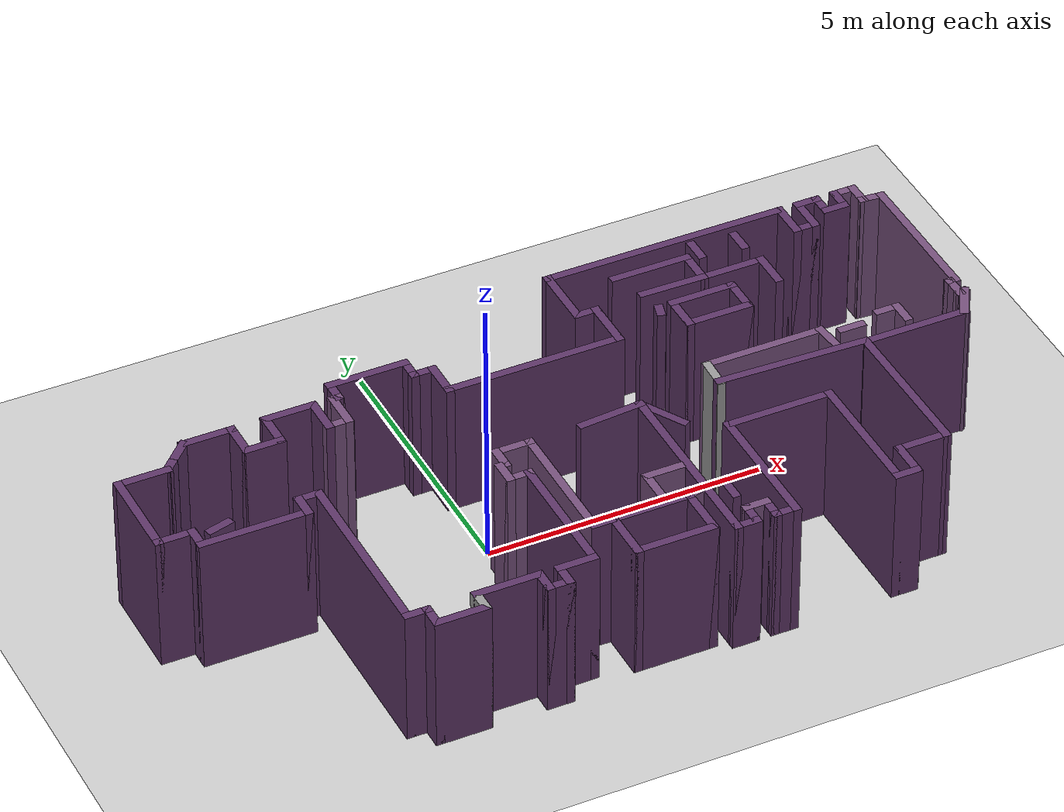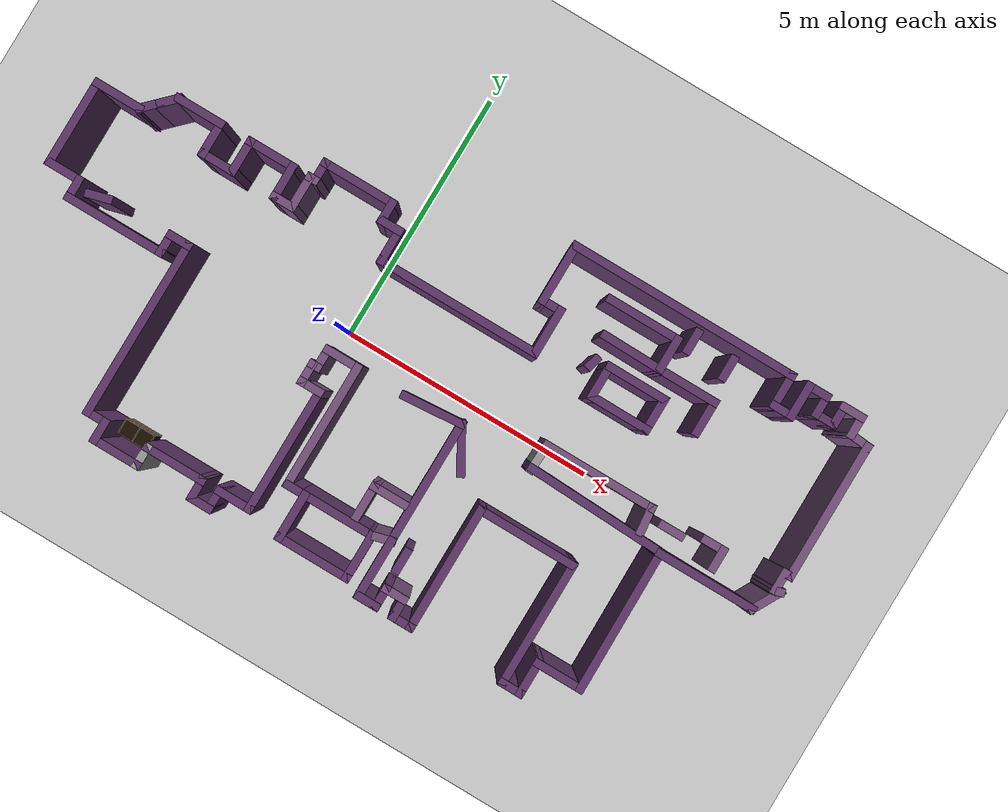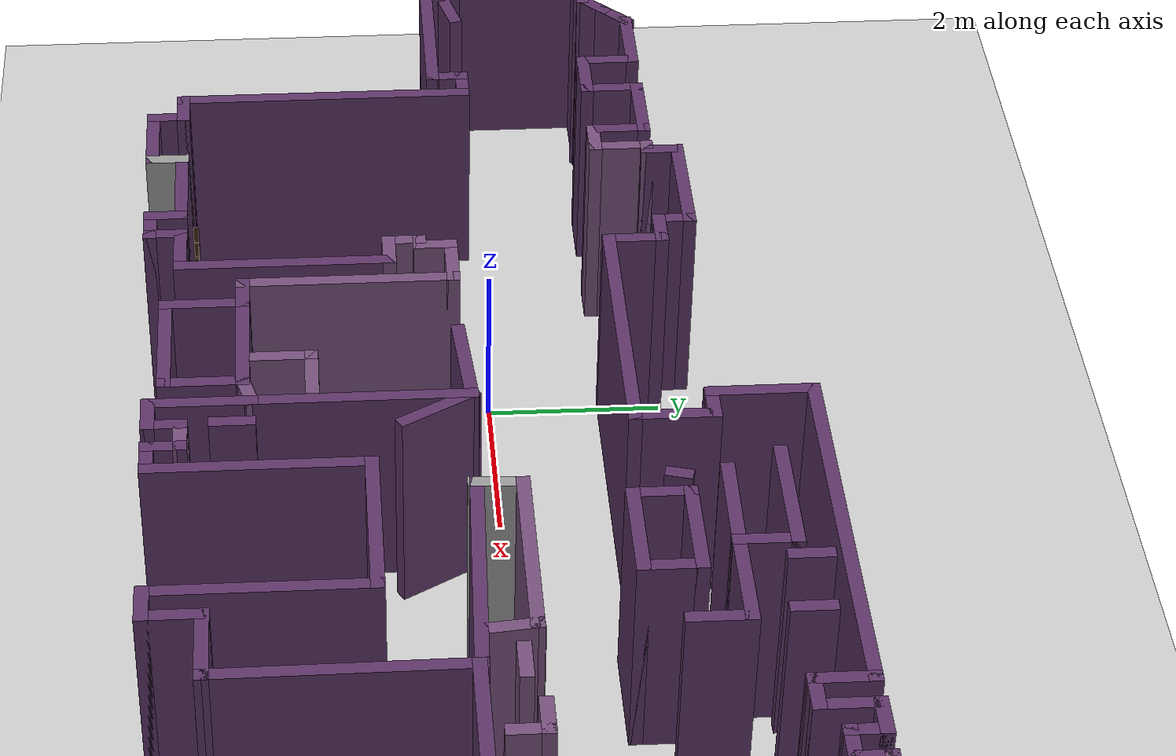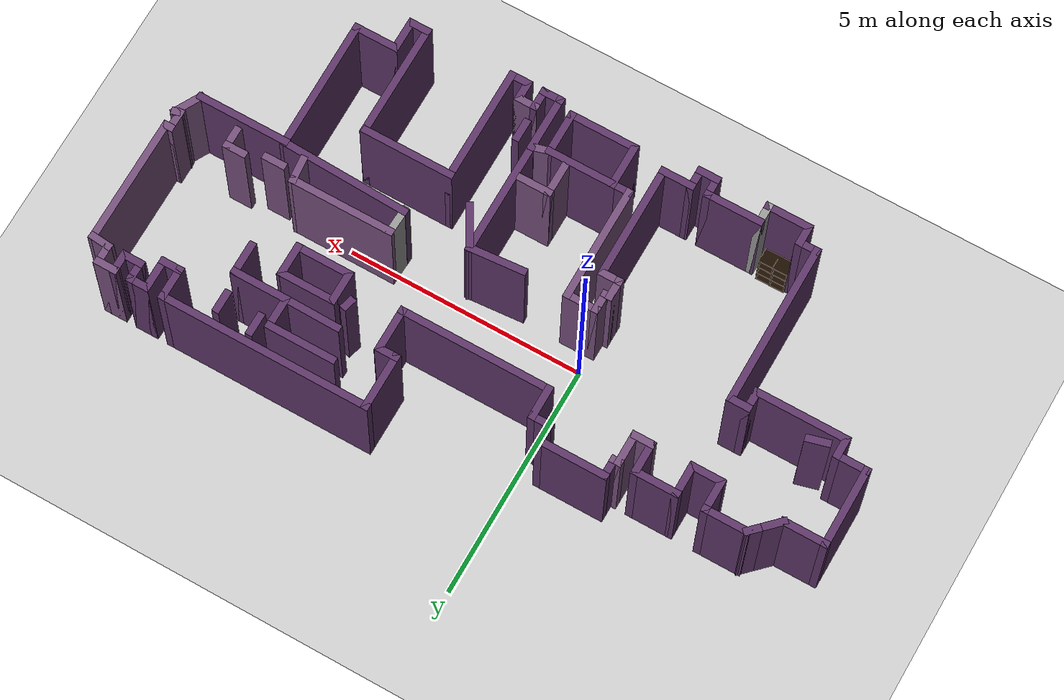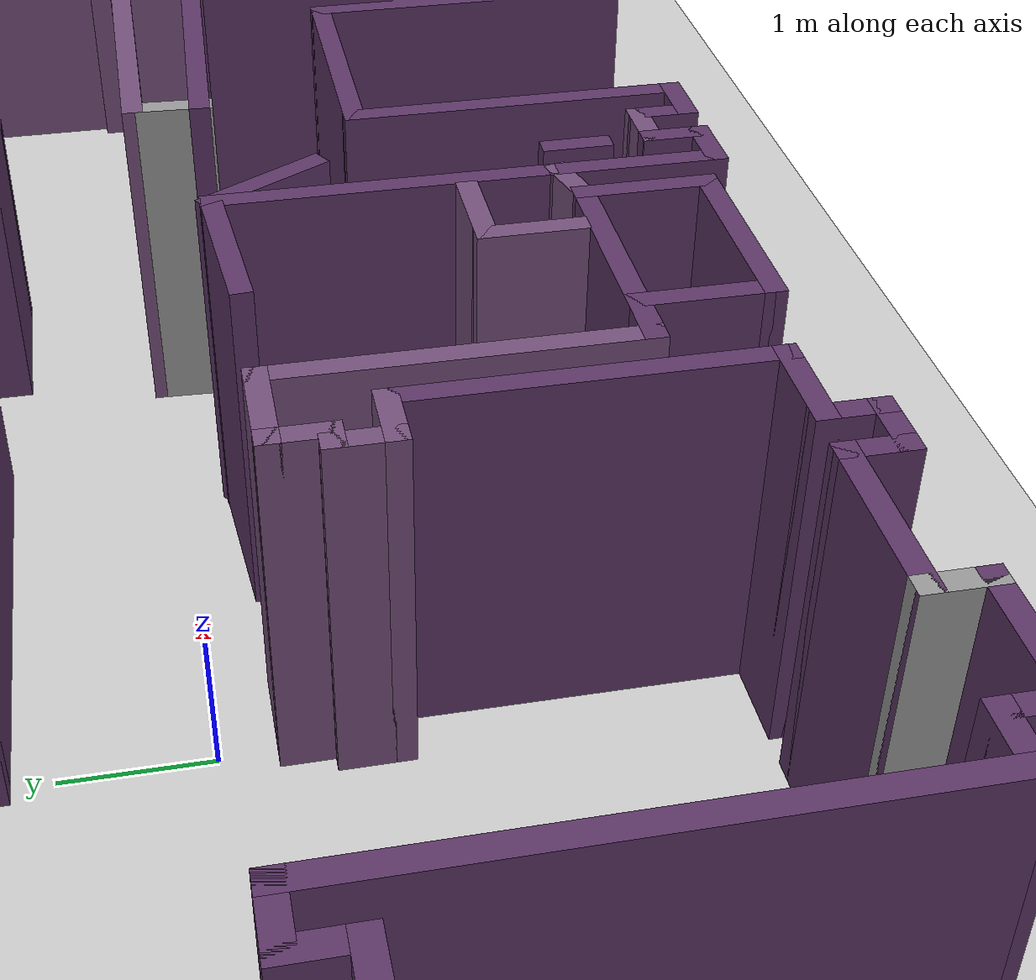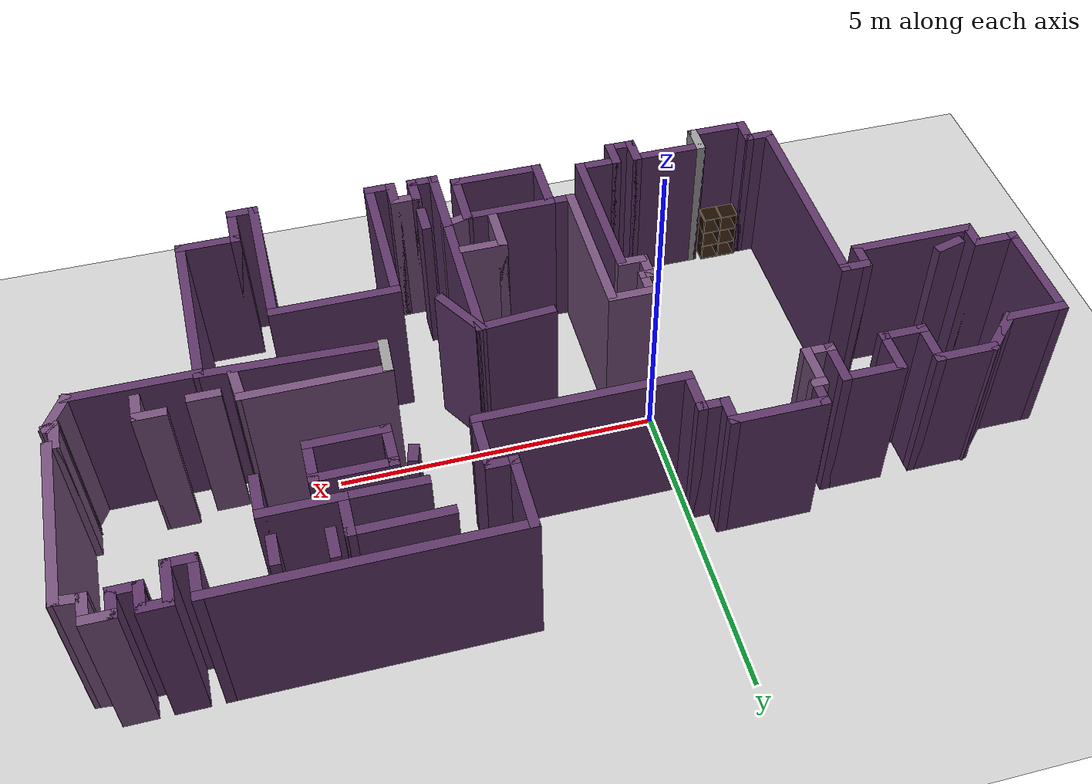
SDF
<sdf version="1.6">
 <world name="default">
  <light name="sun" type="directional">
   <pose>0 0 10 0 -0 0</pose>
   <diffuse>0.8 0.8 0.8 1</diffuse>
   <specular>0.2 0.2 0.2 1</specular>
   <attenuation>
    <range>1000</range>
    <constant>0.9</constant>
    <linear>0.01</linear>
    <quadratic>0.001</quadratic>
   </attenuation>
   <direction>-0.5 0.1 -0.9</direction>
  </light>
  <model name="ground_plane">
   <static>1</static>
   <link name="link">
    <collision name="collision">
     <geometry><plane><normal>0 0 1</normal><size>100 100</size></plane></geometry>
     <surface>
      <contact><collide_bitmask>65535</collide_bitmask></contact>
      <friction><ode><mu>100</mu><mu2>50</mu2></ode></friction>
     </surface>
    </collision>
    <visual name="visual">
     <cast_shadows>0</cast_shadows>
     <geometry><plane><normal>0 0 1</normal><size>100 100</size></plane></geometry>
     <material>
      <script><uri>file://media/materials/scripts/gazebo.material</uri><name>Gazebo/Grey</name></script>
     </material>
    </visual>
   </link>
  </model>
  <gravity>0 0 -9.8</gravity>
  <magnetic_field>6e-06 2.3e-05 -4.2e-05</magnetic_field>
  <atmosphere type="adiabatic"/>
  <physics name="default_physics" default="0" type="ode">
   <max_step_size>0.001</max_step_size>
   <real_time_factor>1</real_time_factor>
   <real_time_update_rate>1000</real_time_update_rate>
  </physics>
  <scene><ambient>0.4 0.4 0.4 1</ambient><background>0.7 0.7 0.7 1</background><shadows>1</shadows></scene>
  <audio><device>default</device></audio>
  <spherical_coordinates>
   <surface_model>EARTH_WGS84</surface_model>
   <latitude_deg>0</latitude_deg>
   <longitude_deg>0</longitude_deg>
   <elevation>0</elevation>
   <heading_deg>0</heading_deg>
  </spherical_coordinates>
  <model name="map_35">
   <pose>1.49139 -0.27307 0 0 -0 0</pose>
   <link name="Wall_0">
    <collision name="Wall_0_Collision">
     <geometry><box><size>4.5 0.15 2.5</size></box></geometry>
     <pose>0 0 1.25 0 -0 0</pose>
    </collision>
    <visual name="Wall_0_Visual">
     <pose>0 0 1.25 0 -0 0</pose>
     <geometry><box><size>4.5 0.15 2.5</size></box></geometry>
     <material>
      <script><uri>file://media/materials/scripts/gazebo.material</uri><name>Gazebo/Grey</name></script>
      <ambient>0.360784 0.207843 0.4 1</ambient>
     </material>
     <meta><layer>0</layer></meta>
    </visual>
    <pose>3.38761 3.57249 0 0 -0 3.14159</pose>
   </link>
   <link name="Wall_1">
    <collision name="Wall_1_Collision">
     <geometry><box><size>1.25 0.15 2.5</size></box></geometry>
     <pose>0 0 1.25 0 -0 0</pose>
    </collision>
    <visual name="Wall_1_Visual">
     <pose>0 0 1.25 0 -0 0</pose>
     <geometry><box><size>1.25 0.15 2.5</size></box></geometry>
     <material>
      <script><uri>file://media/materials/scripts/gazebo.material</uri><name>Gazebo/Grey</name></script>
      <ambient>0.360784 0.207843 0.4 1</ambient>
     </material>
     <meta><layer>0</layer></meta>
    </visual>
    <pose>1.21261 3.02249 0 0 -0 -1.5708</pose>
   </link>
   <link name="Wall_10">
    <collision name="Wall_10_Collision">
     <geometry><box><size>1.5 0.15 2.5</size></box></geometry>
     <pose>0 0 1.25 0 -0 0</pose>
    </collision>
    <visual name="Wall_10_Visual">
     <pose>0 0 1.25 0 -0 0</pose>
     <geometry><box><size>1.5 0.15 2.5</size></box></geometry>
     <material>
      <script><uri>file://media/materials/scripts/gazebo.material</uri><name>Gazebo/Grey</name></script>
      <ambient>0.360784 0.207843 0.4 1</ambient>
     </material>
     <meta><layer>0</layer></meta>
    </visual>
    <pose>-2.56239 2.57249 0 0 -0 3.14159</pose>
   </link>
   <link name="Wall_103">
    <collision name="Wall_103_Collision">
     <geometry><box><size>2 0.15 2.5</size></box></geometry>
     <pose>0 0 1.25 0 -0 0</pose>
    </collision>
    <visual name="Wall_103_Visual">
     <pose>0 0 1.25 0 -0 0</pose>
     <geometry><box><size>2 0.15 2.5</size></box></geometry>
     <material>
      <script><uri>file://media/materials/scripts/gazebo.material</uri><name>Gazebo/Grey</name></script>
      <ambient>0.360784 0.207843 0.4 1</ambient>
     </material>
     <meta><layer>0</layer></meta>
    </visual>
    <pose>6.1106 -0.231333 0 0 -0 0</pose>
   </link>
   <link name="Wall_104">
    <collision name="Wall_104_Collision">
     <geometry><box><size>0.717797 0.15 2.5</size></box></geometry>
     <pose>0 0 1.25 0 -0 0</pose>
    </collision>
    <visual name="Wall_104_Visual">
     <pose>0 0 1.25 0 -0 0</pose>
     <geometry><box><size>0.717797 0.15 2.5</size></box></geometry>
     <material>
      <script><uri>file://media/materials/scripts/gazebo.material</uri><name>Gazebo/Grey</name></script>
      <ambient>0.458824 0.313726 0.482353 1</ambient>
     </material>
     <meta><layer>0</layer></meta>
    </visual>
    <pose>7.17066 0.018383 0 0 -0 1.07501</pose>
   </link>
   <link name="Wall_105">
    <collision name="Wall_105_Collision">
     <geometry><box><size>0.25 0.15 2.5</size></box></geometry>
     <pose>0 0 1.25 0 -0 0</pose>
    </collision>
    <visual name="Wall_105_Visual">
     <pose>0 0 1.25 0 -0 0</pose>
     <geometry><box><size>0.25 0.15 2.5</size></box></geometry>
     <material>
      <script><uri>file://media/materials/scripts/gazebo.material</uri><name>Gazebo/Grey</name></script>
      <ambient>0.458824 0.313726 0.482353 1</ambient>
     </material>
     <meta><layer>0</layer></meta>
    </visual>
    <pose>7.25742 0.255158 0 0 -0 -2.87979</pose>
   </link>
   <link name="Wall_106">
    <collision name="Wall_106_Collision">
     <geometry><box><size>0.5 0.15 2.5</size></box></geometry>
     <pose>0 0 1.25 0 -0 0</pose>
    </collision>
    <visual name="Wall_106_Visual">
     <pose>0 0 1.25 0 -0 0</pose>
     <geometry><box><size>0.5 0.15 2.5</size></box></geometry>
     <material>
      <script><uri>file://media/materials/scripts/gazebo.material</uri><name>Gazebo/Grey</name></script>
      <ambient>0.458824 0.313726 0.482353 1</ambient>
     </material>
     <meta><layer>0</layer></meta>
    </visual>
    <pose>7.20912 0.417217 0 0 -0 1.5708</pose>
   </link>
   <link name="Wall_107">
    <collision name="Wall_107_Collision">
     <geometry><box><size>0.25 0.15 2.5</size></box></geometry>
     <pose>0 0 1.25 0 -0 0</pose>
    </collision>
    <visual name="Wall_107_Visual">
     <pose>0 0 1.25 0 -0 0</pose>
     <geometry><box><size>0.25 0.15 2.5</size></box></geometry>
     <material>
      <script><uri>file://media/materials/scripts/gazebo.material</uri><name>Gazebo/Grey</name></script>
      <ambient>0.458824 0.313726 0.482353 1</ambient>
     </material>
     <meta><layer>0</layer></meta>
    </visual>
    <pose>7.25912 0.592217 0 0 -0 0</pose>
   </link>
   <link name="Wall_108">
    <collision name="Wall_108_Collision">
     <geometry><box><size>2.75 0.15 2.5</size></box></geometry>
     <pose>0 0 1.25 0 -0 0</pose>
    </collision>
    <visual name="Wall_108_Visual">
     <pose>0 0 1.25 0 -0 0</pose>
     <geometry><box><size>2.75 0.15 2.5</size></box></geometry>
     <material>
      <script><uri>file://media/materials/scripts/gazebo.material</uri><name>Gazebo/Grey</name></script>
      <ambient>0.458824 0.313726 0.482353 1</ambient>
     </material>
     <meta><layer>0</layer></meta>
    </visual>
    <pose>7.30912 1.89222 0 0 -0 1.5708</pose>
   </link>
   <link name="Wall_11">
    <collision name="Wall_11_Collision">
     <geometry><box><size>0.5 0.15 2.5</size></box></geometry>
     <pose>0 0 1.25 0 -0 0</pose>
    </collision>
    <visual name="Wall_11_Visual">
     <pose>0 0 1.25 0 -0 0</pose>
     <geometry><box><size>0.5 0.15 2.5</size></box></geometry>
     <material>
      <script><uri>file://media/materials/scripts/gazebo.material</uri><name>Gazebo/Grey</name></script>
      <ambient>0.360784 0.207843 0.4 1</ambient>
     </material>
     <meta><layer>0</layer></meta>
    </visual>
    <pose>-3.23739 2.39749 0 0 -0 -1.5708</pose>
   </link>
   <link name="Wall_115">
    <collision name="Wall_115_Collision">
     <geometry><box><size>0.75 0.15 2.5</size></box></geometry>
     <pose>0 0 1.25 0 -0 0</pose>
    </collision>
    <visual name="Wall_115_Visual">
     <pose>0 0 1.25 0 -0 0</pose>
     <geometry><box><size>0.75 0.15 2.5</size></box></geometry>
     <material>
      <script><uri>file://media/materials/scripts/gazebo.material</uri><name>Gazebo/Grey</name></script>
      <ambient>0.360784 0.207843 0.4 1</ambient>
     </material>
     <meta><layer>0</layer></meta>
    </visual>
    <pose>5.56261 3.27249 0 0 -0 -1.5708</pose>
   </link>
   <link name="Wall_116">
    <collision name="Wall_116_Collision">
     <geometry><box><size>0.5 0.15 2.5</size></box></geometry>
     <pose>0 0 1.25 0 -0 0</pose>
    </collision>
    <visual name="Wall_116_Visual">
     <pose>0 0 1.25 0 -0 0</pose>
     <geometry><box><size>0.5 0.15 2.5</size></box></geometry>
     <material>
      <script><uri>file://media/materials/scripts/gazebo.material</uri><name>Gazebo/Grey</name></script>
      <ambient>0.360784 0.207843 0.4 1</ambient>
     </material>
     <meta><layer>0</layer></meta>
    </visual>
    <pose>5.73761 2.97249 0 0 -0 0</pose>
   </link>
   <link name="Wall_119">
    <collision name="Wall_119_Collision">
     <geometry><box><size>0.75 0.15 2.5</size></box></geometry>
     <pose>0 0 1.25 0 -0 0</pose>
    </collision>
    <visual name="Wall_119_Visual">
     <pose>0 0 1.25 0 -0 0</pose>
     <geometry><box><size>0.75 0.15 2.5</size></box></geometry>
     <material>
      <script><uri>file://media/materials/scripts/gazebo.material</uri><name>Gazebo/Grey</name></script>
      <ambient>0.360784 0.207843 0.4 1</ambient>
     </material>
     <meta><layer>0</layer></meta>
    </visual>
    <pose>5.91261 3.27249 0 0 -0 1.5708</pose>
   </link>
   <link name="Wall_12">
    <collision name="Wall_12_Collision">
     <geometry><box><size>0.25 0.15 2.5</size></box></geometry>
     <pose>0 0 1.25 0 -0 0</pose>
    </collision>
    <visual name="Wall_12_Visual">
     <pose>0 0 1.25 0 -0 0</pose>
     <geometry><box><size>0.25 0.15 2.5</size></box></geometry>
     <material>
      <script><uri>file://media/materials/scripts/gazebo.material</uri><name>Gazebo/Grey</name></script>
      <ambient>0.458824 0.313726 0.482353 1</ambient>
     </material>
     <meta><layer>0</layer></meta>
    </visual>
    <pose>-3.28739 2.22249 0 0 -0 3.14159</pose>
   </link>
   <link name="Wall_120">
    <collision name="Wall_120_Collision">
     <geometry><box><size>0.5 0.15 2.5</size></box></geometry>
     <pose>0 0 1.25 0 -0 0</pose>
    </collision>
    <visual name="Wall_120_Visual">
     <pose>0 0 1.25 0 -0 0</pose>
     <geometry><box><size>0.5 0.15 2.5</size></box></geometry>
     <material>
      <script><uri>file://media/materials/scripts/gazebo.material</uri><name>Gazebo/Grey</name></script>
      <ambient>0.360784 0.207843 0.4 1</ambient>
     </material>
     <meta><layer>0</layer></meta>
    </visual>
    <pose>6.08761 3.57249 0 0 -0 0</pose>
   </link>
   <link name="Wall_121">
    <collision name="Wall_121_Collision">
     <geometry><box><size>0.5 0.15 2.5</size></box></geometry>
     <pose>0 0 1.25 0 -0 0</pose>
    </collision>
    <visual name="Wall_121_Visual">
     <pose>0 0 1.25 0 -0 0</pose>
     <geometry><box><size>0.5 0.15 2.5</size></box></geometry>
     <material>
      <script><uri>file://media/materials/scripts/gazebo.material</uri><name>Gazebo/Grey</name></script>
      <ambient>0.360784 0.207843 0.4 1</ambient>
     </material>
     <meta><layer>0</layer></meta>
    </visual>
    <pose>6.26261 3.39749 0 0 -0 -1.5708</pose>
   </link>
   <link name="Wall_122">
    <collision name="Wall_122_Collision">
     <geometry><box><size>0.5 0.15 2.5</size></box></geometry>
     <pose>0 0 1.25 0 -0 0</pose>
    </collision>
    <visual name="Wall_122_Visual">
     <pose>0 0 1.25 0 -0 0</pose>
     <geometry><box><size>0.5 0.15 2.5</size></box></geometry>
     <material>
      <script><uri>file://media/materials/scripts/gazebo.material</uri><name>Gazebo/Grey</name></script>
      <ambient>0.360784 0.207843 0.4 1</ambient>
     </material>
     <meta><layer>0</layer></meta>
    </visual>
    <pose>6.43761 3.22249 0 0 -0 0</pose>
   </link>
   <link name="Wall_123">
    <collision name="Wall_123_Collision">
     <geometry><box><size>0.5 0.15 2.5</size></box></geometry>
     <pose>0 0 1.25 0 -0 0</pose>
    </collision>
    <visual name="Wall_123_Visual">
     <pose>0 0 1.25 0 -0 0</pose>
     <geometry><box><size>0.5 0.15 2.5</size></box></geometry>
     <material>
      <script><uri>file://media/materials/scripts/gazebo.material</uri><name>Gazebo/Grey</name></script>
      <ambient>0.360784 0.207843 0.4 1</ambient>
     </material>
     <meta><layer>0</layer></meta>
    </visual>
    <pose>6.61261 3.39749 0 0 -0 1.5708</pose>
   </link>
   <link name="Wall_124">
    <collision name="Wall_124_Collision">
     <geometry><box><size>0.5 0.15 2.5</size></box></geometry>
     <pose>0 0 1.25 0 -0 0</pose>
    </collision>
    <visual name="Wall_124_Visual">
     <pose>0 0 1.25 0 -0 0</pose>
     <geometry><box><size>0.5 0.15 2.5</size></box></geometry>
     <material>
      <script><uri>file://media/materials/scripts/gazebo.material</uri><name>Gazebo/Grey</name></script>
      <ambient>0.458824 0.313726 0.482353 1</ambient>
     </material>
     <meta><layer>0</layer></meta>
    </visual>
    <pose>6.78761 3.57249 0 0 -0 0</pose>
   </link>
   <link name="Wall_125">
    <collision name="Wall_125_Collision">
     <geometry><box><size>0.5 0.15 2.5</size></box></geometry>
     <pose>0 0 1.25 0 -0 0</pose>
    </collision>
    <visual name="Wall_125_Visual">
     <pose>0 0 1.25 0 -0 0</pose>
     <geometry><box><size>0.5 0.15 2.5</size></box></geometry>
     <material>
      <script><uri>file://media/materials/scripts/gazebo.material</uri><name>Gazebo/Grey</name></script>
      <ambient>0.458824 0.313726 0.482353 1</ambient>
     </material>
     <meta><layer>0</layer></meta>
    </visual>
    <pose>6.96261 3.39749 0 0 -0 -1.5708</pose>
   </link>
   <link name="Wall_126">
    <collision name="Wall_126_Collision">
     <geometry><box><size>0.497826 0.15 2.5</size></box></geometry>
     <pose>0 0 1.25 0 -0 0</pose>
    </collision>
    <visual name="Wall_126_Visual">
     <pose>0 0 1.25 0 -0 0</pose>
     <geometry><box><size>0.497826 0.15 2.5</size></box></geometry>
     <material>
      <script><uri>file://media/materials/scripts/gazebo.material</uri><name>Gazebo/Grey</name></script>
      <ambient>0.458824 0.313726 0.482353 1</ambient>
     </material>
     <meta><layer>0</layer></meta>
    </visual>
    <pose>7.13587 3.20735 0 0 -0 -0.087136</pose>
   </link>
   <link name="Wall_128">
    <collision name="Wall_128_Collision">
     <geometry><box><size>0.75 0.15 2.5</size></box></geometry>
     <pose>0 0 1.25 0 -0 0</pose>
    </collision>
    <visual name="Wall_128_Visual">
     <pose>0 0 1.25 0 -0 0</pose>
     <geometry><box><size>0.75 0.15 2.5</size></box></geometry>
     <material>
      <script><uri>file://media/materials/scripts/gazebo.material</uri><name>Gazebo/Grey</name></script>
      <ambient>0.360784 0.207843 0.4 1</ambient>
     </material>
     <meta><layer>0</layer></meta>
    </visual>
    <pose>2.78694 1.78408 0 0 -0 -1.5708</pose>
   </link>
   <link name="Wall_129">
    <collision name="Wall_129_Collision">
     <geometry><box><size>1.25 0.15 2.5</size></box></geometry>
     <pose>0 0 1.25 0 -0 0</pose>
    </collision>
    <visual name="Wall_129_Visual">
     <pose>0 0 1.25 0 -0 0</pose>
     <geometry><box><size>1.25 0.15 2.5</size></box></geometry>
     <material>
      <script><uri>file://media/materials/scripts/gazebo.material</uri><name>Gazebo/Grey</name></script>
      <ambient>0.360784 0.207843 0.4 1</ambient>
     </material>
     <meta><layer>0</layer></meta>
    </visual>
    <pose>3.33694 1.48408 0 0 -0 0</pose>
   </link>
   <link name="Wall_13">
    <collision name="Wall_13_Collision">
     <geometry><box><size>0.75 0.15 2.5</size></box></geometry>
     <pose>0 0 1.25 0 -0 0</pose>
    </collision>
    <visual name="Wall_13_Visual">
     <pose>0 0 1.25 0 -0 0</pose>
     <geometry><box><size>0.75 0.15 2.5</size></box></geometry>
     <material>
      <script><uri>file://media/materials/scripts/gazebo.material</uri><name>Gazebo/Grey</name></script>
      <ambient>0.458824 0.313726 0.482353 1</ambient>
     </material>
     <meta><layer>0</layer></meta>
    </visual>
    <pose>-3.33739 1.92249 0 0 -0 -1.5708</pose>
   </link>
   <link name="Wall_130">
    <collision name="Wall_130_Collision">
     <geometry><box><size>0.75 0.15 2.5</size></box></geometry>
     <pose>0 0 1.25 0 -0 0</pose>
    </collision>
    <visual name="Wall_130_Visual">
     <pose>0 0 1.25 0 -0 0</pose>
     <geometry><box><size>0.75 0.15 2.5</size></box></geometry>
     <material>
      <script><uri>file://media/materials/scripts/gazebo.material</uri><name>Gazebo/Grey</name></script>
      <ambient>0.360784 0.207843 0.4 1</ambient>
     </material>
     <meta><layer>0</layer></meta>
    </visual>
    <pose>3.88694 1.78408 0 0 -0 1.5708</pose>
   </link>
   <link name="Wall_131">
    <collision name="Wall_131_Collision">
     <geometry><box><size>1.25 0.15 2.5</size></box></geometry>
     <pose>0 0 1.25 0 -0 0</pose>
    </collision>
    <visual name="Wall_131_Visual">
     <pose>0 0 1.25 0 -0 0</pose>
     <geometry><box><size>1.25 0.15 2.5</size></box></geometry>
     <material>
      <script><uri>file://media/materials/scripts/gazebo.material</uri><name>Gazebo/Grey</name></script>
      <ambient>0.360784 0.207843 0.4 1</ambient>
     </material>
     <meta><layer>0</layer></meta>
    </visual>
    <pose>3.33694 2.08408 0 0 -0 3.14159</pose>
   </link>
   <link name="Wall_133">
    <collision name="Wall_133_Collision">
     <geometry><box><size>0.3 0.15 2.5</size></box></geometry>
     <pose>0 0 1.25 0 -0 0</pose>
    </collision>
    <visual name="Wall_133_Visual">
     <pose>0 0 1.25 0 -0 0</pose>
     <geometry><box><size>0.3 0.15 2.5</size></box></geometry>
     <material>
      <script><uri>file://media/materials/scripts/gazebo.material</uri><name>Gazebo/Grey</name></script>
      <ambient>0.360784 0.207843 0.4 1</ambient>
     </material>
     <meta><layer>0</layer></meta>
    </visual>
    <pose>2.50465 1.99562 0 0 -0 1.309</pose>
   </link>
   <link name="Wall_135">
    <collision name="Wall_135_Collision">
     <geometry><box><size>1.5 0.15 2.5</size></box></geometry>
     <pose>0 0 1.25 0 -0 0</pose>
    </collision>
    <visual name="Wall_135_Visual">
     <pose>0 0 1.25 0 -0 0</pose>
     <geometry><box><size>1.5 0.15 2.5</size></box></geometry>
     <material>
      <script><uri>file://media/materials/scripts/gazebo.material</uri><name>Gazebo/Grey</name></script>
      <ambient>0.360784 0.207843 0.4 1</ambient>
     </material>
     <meta><layer>0</layer></meta>
    </visual>
    <pose>2.87865 3.08976 0 0 -0 0</pose>
   </link>
   <link name="Wall_136">
    <collision name="Wall_136_Collision">
     <geometry><box><size>0.75 0.15 2.5</size></box></geometry>
     <pose>0 0 1.25 0 -0 0</pose>
    </collision>
    <visual name="Wall_136_Visual">
     <pose>0 0 1.25 0 -0 0</pose>
     <geometry><box><size>0.75 0.15 2.5</size></box></geometry>
     <material>
      <script><uri>file://media/materials/scripts/gazebo.material</uri><name>Gazebo/Grey</name></script>
      <ambient>0.360784 0.207843 0.4 1</ambient>
     </material>
     <meta><layer>0</layer></meta>
    </visual>
    <pose>3.55365 2.78976 0 0 -0 -1.5708</pose>
   </link>
   <link name="Wall_137">
    <collision name="Wall_137_Collision">
     <geometry><box><size>1.25 0.15 2.5</size></box></geometry>
     <pose>0 0 1.25 0 -0 0</pose>
    </collision>
    <visual name="Wall_137_Visual">
     <pose>0 0 1.25 0 -0 0</pose>
     <geometry><box><size>1.25 0.15 2.5</size></box></geometry>
     <material>
      <script><uri>file://media/materials/scripts/gazebo.material</uri><name>Gazebo/Grey</name></script>
      <ambient>0.360784 0.207843 0.4 1</ambient>
     </material>
     <meta><layer>0</layer></meta>
    </visual>
    <pose>4.10365 2.48976 0 0 -0 0</pose>
   </link>
   <link name="Wall_138">
    <collision name="Wall_138_Collision">
     <geometry><box><size>0.75 0.15 2.5</size></box></geometry>
     <pose>0 0 1.25 0 -0 0</pose>
    </collision>
    <visual name="Wall_138_Visual">
     <pose>0 0 1.25 0 -0 0</pose>
     <geometry><box><size>0.75 0.15 2.5</size></box></geometry>
     <material>
      <script><uri>file://media/materials/scripts/gazebo.material</uri><name>Gazebo/Grey</name></script>
      <ambient>0.360784 0.207843 0.4 1</ambient>
     </material>
     <meta><layer>0</layer></meta>
    </visual>
    <pose>4.65365 2.18976 0 0 -0 -1.5708</pose>
   </link>
   <link name="Wall_14">
    <collision name="Wall_14_Collision">
     <geometry><box><size>0.5 0.15 2.5</size></box></geometry>
     <pose>0 0 1.25 0 -0 0</pose>
    </collision>
    <visual name="Wall_14_Visual">
     <pose>0 0 1.25 0 -0 0</pose>
     <geometry><box><size>0.5 0.15 2.5</size></box></geometry>
     <material>
      <script><uri>file://media/materials/scripts/gazebo.material</uri><name>Gazebo/Grey</name></script>
      <ambient>0.458824 0.313726 0.482353 1</ambient>
     </material>
     <meta><layer>0</layer></meta>
    </visual>
    <pose>-3.51239 1.62249 0 0 -0 3.14159</pose>
   </link>
   <link name="Wall_140">
    <collision name="Wall_140_Collision">
     <geometry><box><size>1.25876 0.15 2.5</size></box></geometry>
     <pose>0 0 1.25 0 -0 0</pose>
    </collision>
    <visual name="Wall_140_Visual">
     <pose>0 0 1.25 0 -0 0</pose>
     <geometry><box><size>1.25876 0.15 2.5</size></box></geometry>
     <material>
      <script><uri>file://media/materials/scripts/gazebo.material</uri><name>Gazebo/Grey</name></script>
      <ambient>0.360784 0.207843 0.4 1</ambient>
     </material>
     <meta><layer>0</layer></meta>
    </visual>
    <pose>2.99933 2.49811 0 0 -0 -0.015068</pose>
   </link>
   <link name="Wall_142">
    <collision name="Wall_142_Collision">
     <geometry><box><size>0.5 0.15 2.5</size></box></geometry>
     <pose>0 0 1.25 0 -0 0</pose>
    </collision>
    <visual name="Wall_142_Visual">
     <pose>0 0 1.25 0 -0 0</pose>
     <geometry><box><size>0.5 0.15 2.5</size></box></geometry>
     <material>
      <script><uri>file://media/materials/scripts/gazebo.material</uri><name>Gazebo/Grey</name></script>
      <ambient>0.360784 0.207843 0.4 1</ambient>
     </material>
     <meta><layer>0</layer></meta>
    </visual>
    <pose>3.79262 3.19635 0 0 -0 -1.5708</pose>
   </link>
   <link name="Wall_144">
    <collision name="Wall_144_Collision">
     <geometry><box><size>0.5 0.15 2.5</size></box></geometry>
     <pose>0 0 1.25 0 -0 0</pose>
    </collision>
    <visual name="Wall_144_Visual">
     <pose>0 0 1.25 0 -0 0</pose>
     <geometry><box><size>0.5 0.15 2.5</size></box></geometry>
     <material>
      <script><uri>file://media/materials/scripts/gazebo.material</uri><name>Gazebo/Grey</name></script>
      <ambient>0.360784 0.207843 0.4 1</ambient>
     </material>
     <meta><layer>0</layer></meta>
    </visual>
    <pose>4.55693 3.1159 0 0 -0 -1.5708</pose>
   </link>
   <link name="Wall_146">
    <collision name="Wall_146_Collision">
     <geometry><box><size>0.5 0.15 2.5</size></box></geometry>
     <pose>0 0 1.25 0 -0 0</pose>
    </collision>
    <visual name="Wall_146_Visual">
     <pose>0 0 1.25 0 -0 0</pose>
     <geometry><box><size>0.5 0.15 2.5</size></box></geometry>
     <material>
      <script><uri>file://media/materials/scripts/gazebo.material</uri><name>Gazebo/Grey</name></script>
      <ambient>0.458824 0.313726 0.482353 1</ambient>
     </material>
     <meta><layer>0</layer></meta>
    </visual>
    <pose>5.15432 0.213521 0 0 -0 0</pose>
   </link>
   <link name="Wall_150">
    <collision name="Wall_150_Collision">
     <geometry><box><size>0.5 0.15 2.5</size></box></geometry>
     <pose>0 0 1.25 0 -0 0</pose>
    </collision>
    <visual name="Wall_150_Visual">
     <pose>0 0 1.25 0 -0 0</pose>
     <geometry><box><size>0.5 0.15 2.5</size></box></geometry>
     <material>
      <script><uri>file://media/materials/scripts/gazebo.material</uri><name>Gazebo/Grey</name></script>
      <ambient>0.458824 0.313726 0.482353 1</ambient>
     </material>
     <meta><layer>0</layer></meta>
    </visual>
    <pose>5.91864 0.37443 0 0 -0 0</pose>
   </link>
   <link name="Wall_151">
    <collision name="Wall_151_Collision">
     <geometry><box><size>0.5 0.15 2.5</size></box></geometry>
     <pose>0 0 1.25 0 -0 0</pose>
    </collision>
    <visual name="Wall_151_Visual">
     <pose>0 0 1.25 0 -0 0</pose>
     <geometry><box><size>0.5 0.15 2.5</size></box></geometry>
     <material>
      <script><uri>file://media/materials/scripts/gazebo.material</uri><name>Gazebo/Grey</name></script>
      <ambient>0.458824 0.313726 0.482353 1</ambient>
     </material>
     <meta><layer>0</layer></meta>
    </visual>
    <pose>6.09363 0.199429 0 0 -0 -1.5708</pose>
   </link>
   <link name="Wall_153">
    <collision name="Wall_153_Collision">
     <geometry><box><size>0.5 0.15 2.5</size></box></geometry>
     <pose>0 0 1.25 0 -0 0</pose>
    </collision>
    <visual name="Wall_153_Visual">
     <pose>0 0 1.25 0 -0 0</pose>
     <geometry><box><size>0.5 0.15 2.5</size></box></geometry>
     <material>
      <script><uri>file://media/materials/scripts/gazebo.material</uri><name>Gazebo/Grey</name></script>
      <ambient>0.360784 0.207843 0.4 1</ambient>
     </material>
     <meta><layer>0</layer></meta>
    </visual>
    <pose>1.43933 -2.63658 0 0 -0 -1.5708</pose>
   </link>
   <link name="Wall_155">
    <collision name="Wall_155_Collision">
     <geometry><box><size>0.5 0.15 2.5</size></box></geometry>
     <pose>0 0 1.25 0 -0 0</pose>
    </collision>
    <visual name="Wall_155_Visual">
     <pose>0 0 1.25 0 -0 0</pose>
     <geometry><box><size>0.5 0.15 2.5</size></box></geometry>
     <material>
      <script><uri>file://media/materials/scripts/gazebo.material</uri><name>Gazebo/Grey</name></script>
      <ambient>0.360784 0.207843 0.4 1</ambient>
     </material>
     <meta><layer>0</layer></meta>
    </visual>
    <pose>-6.29627 0.057679 0 0 -0 0.261799</pose>
   </link>
   <link name="Wall_17">
    <collision name="Wall_17_Collision">
     <geometry><box><size>0.75 0.15 2.5</size></box></geometry>
     <pose>0 0 1.25 0 -0 0</pose>
    </collision>
    <visual name="Wall_17_Visual">
     <pose>0 0 1.25 0 -0 0</pose>
     <geometry><box><size>0.75 0.15 2.5</size></box></geometry>
     <material>
      <script><uri>file://media/materials/scripts/gazebo.material</uri><name>Gazebo/Grey</name></script>
      <ambient>0.360784 0.207843 0.4 1</ambient>
     </material>
     <meta><layer>0</layer></meta>
    </visual>
    <pose>-3.68739 1.92249 0 0 -0 1.5708</pose>
   </link>
   <link name="Wall_18">
    <collision name="Wall_18_Collision">
     <geometry><box><size>1 0.15 2.5</size></box></geometry>
     <pose>0 0 1.25 0 -0 0</pose>
    </collision>
    <visual name="Wall_18_Visual">
     <pose>0 0 1.25 0 -0 0</pose>
     <geometry><box><size>1 0.15 2.5</size></box></geometry>
     <material>
      <script><uri>file://media/materials/scripts/gazebo.material</uri><name>Gazebo/Grey</name></script>
      <ambient>0.360784 0.207843 0.4 1</ambient>
     </material>
     <meta><layer>0</layer></meta>
    </visual>
    <pose>-4.11239 2.22249 0 0 -0 3.14159</pose>
   </link>
   <link name="Wall_19">
    <collision name="Wall_19_Collision">
     <geometry><box><size>0.75 0.15 2.5</size></box></geometry>
     <pose>0 0 1.25 0 -0 0</pose>
    </collision>
    <visual name="Wall_19_Visual">
     <pose>0 0 1.25 0 -0 0</pose>
     <geometry><box><size>0.75 0.15 2.5</size></box></geometry>
     <material>
      <script><uri>file://media/materials/scripts/gazebo.material</uri><name>Gazebo/Grey</name></script>
      <ambient>0.360784 0.207843 0.4 1</ambient>
     </material>
     <meta><layer>0</layer></meta>
    </visual>
    <pose>-4.53739 1.92249 0 0 -0 -1.5708</pose>
   </link>
   <link name="Wall_20">
    <collision name="Wall_20_Collision">
     <geometry><box><size>0.75 0.15 2.5</size></box></geometry>
     <pose>0 0 1.25 0 -0 0</pose>
    </collision>
    <visual name="Wall_20_Visual">
     <pose>0 0 1.25 0 -0 0</pose>
     <geometry><box><size>0.75 0.15 2.5</size></box></geometry>
     <material>
      <script><uri>file://media/materials/scripts/gazebo.material</uri><name>Gazebo/Grey</name></script>
      <ambient>0.360784 0.207843 0.4 1</ambient>
     </material>
     <meta><layer>0</layer></meta>
    </visual>
    <pose>-4.83739 1.62249 0 0 -0 3.14159</pose>
   </link>
   <link name="Wall_21">
    <collision name="Wall_21_Collision">
     <geometry><box><size>0.75 0.15 2.5</size></box></geometry>
     <pose>0 0 1.25 0 -0 0</pose>
    </collision>
    <visual name="Wall_21_Visual">
     <pose>0 0 1.25 0 -0 0</pose>
     <geometry><box><size>0.75 0.15 2.5</size></box></geometry>
     <material>
      <script><uri>file://media/materials/scripts/gazebo.material</uri><name>Gazebo/Grey</name></script>
      <ambient>0.360784 0.207843 0.4 1</ambient>
     </material>
     <meta><layer>0</layer></meta>
    </visual>
    <pose>-5.13739 1.92249 0 0 -0 1.5708</pose>
   </link>
   <link name="Wall_22">
    <collision name="Wall_22_Collision">
     <geometry><box><size>1 0.15 2.5</size></box></geometry>
     <pose>0 0 1.25 0 -0 0</pose>
    </collision>
    <visual name="Wall_22_Visual">
     <pose>0 0 1.25 0 -0 0</pose>
     <geometry><box><size>1 0.15 2.5</size></box></geometry>
     <material>
      <script><uri>file://media/materials/scripts/gazebo.material</uri><name>Gazebo/Grey</name></script>
      <ambient>0.360784 0.207843 0.4 1</ambient>
     </material>
     <meta><layer>0</layer></meta>
    </visual>
    <pose>-5.56239 2.22249 0 0 -0 3.14159</pose>
   </link>
   <link name="Wall_23">
    <collision name="Wall_23_Collision">
     <geometry><box><size>0.5 0.15 2.5</size></box></geometry>
     <pose>0 0 1.25 0 -0 0</pose>
    </collision>
    <visual name="Wall_23_Visual">
     <pose>0 0 1.25 0 -0 0</pose>
     <geometry><box><size>0.5 0.15 2.5</size></box></geometry>
     <material>
      <script><uri>file://media/materials/scripts/gazebo.material</uri><name>Gazebo/Grey</name></script>
      <ambient>0.360784 0.207843 0.4 1</ambient>
     </material>
     <meta><layer>0</layer></meta>
    </visual>
    <pose>-6.11113 2.09874 0 0 -0 -2.35619</pose>
   </link>
   <link name="Wall_24">
    <collision name="Wall_24_Collision">
     <geometry><box><size>0.5 0.15 2.5</size></box></geometry>
     <pose>0 0 1.25 0 -0 0</pose>
    </collision>
    <visual name="Wall_24_Visual">
     <pose>0 0 1.25 0 -0 0</pose>
     <geometry><box><size>0.5 0.15 2.5</size></box></geometry>
     <material>
      <script><uri>file://media/materials/scripts/gazebo.material</uri><name>Gazebo/Grey</name></script>
      <ambient>0.360784 0.207843 0.4 1</ambient>
     </material>
     <meta><layer>0</layer></meta>
    </visual>
    <pose>-6.35862 1.85126 0 0 -0 -2.35619</pose>
   </link>
   <link name="Wall_25">
    <collision name="Wall_25_Collision">
     <geometry><box><size>1 0.15 2.5</size></box></geometry>
     <pose>0 0 1.25 0 -0 0</pose>
    </collision>
    <visual name="Wall_25_Visual">
     <pose>0 0 1.25 0 -0 0</pose>
     <geometry><box><size>1 0.15 2.5</size></box></geometry>
     <material>
      <script><uri>file://media/materials/scripts/gazebo.material</uri><name>Gazebo/Grey</name></script>
      <ambient>0.360784 0.207843 0.4 1</ambient>
     </material>
     <meta><layer>0</layer></meta>
    </visual>
    <pose>-6.90736 1.72751 0 0 -0 3.14159</pose>
   </link>
   <link name="Wall_26">
    <collision name="Wall_26_Collision">
     <geometry><box><size>1.75 0.15 2.5</size></box></geometry>
     <pose>0 0 1.25 0 -0 0</pose>
    </collision>
    <visual name="Wall_26_Visual">
     <pose>0 0 1.25 0 -0 0</pose>
     <geometry><box><size>1.75 0.15 2.5</size></box></geometry>
     <material>
      <script><uri>file://media/materials/scripts/gazebo.material</uri><name>Gazebo/Grey</name></script>
      <ambient>0.360784 0.207843 0.4 1</ambient>
     </material>
     <meta><layer>0</layer></meta>
    </visual>
    <pose>-7.33236 0.927513 0 0 -0 -1.5708</pose>
   </link>
   <link name="Wall_27">
    <collision name="Wall_27_Collision">
     <geometry><box><size>0.75 0.15 2.5</size></box></geometry>
     <pose>0 0 1.25 0 -0 0</pose>
    </collision>
    <visual name="Wall_27_Visual">
     <pose>0 0 1.25 0 -0 0</pose>
     <geometry><box><size>0.75 0.15 2.5</size></box></geometry>
     <material>
      <script><uri>file://media/materials/scripts/gazebo.material</uri><name>Gazebo/Grey</name></script>
      <ambient>0.360784 0.207843 0.4 1</ambient>
     </material>
     <meta><layer>0</layer></meta>
    </visual>
    <pose>-7.03236 0.127513 0 0 -0 0</pose>
   </link>
   <link name="Wall_28">
    <collision name="Wall_28_Collision">
     <geometry><box><size>0.5 0.15 2.5</size></box></geometry>
     <pose>0 0 1.25 0 -0 0</pose>
    </collision>
    <visual name="Wall_28_Visual">
     <pose>0 0 1.25 0 -0 0</pose>
     <geometry><box><size>0.5 0.15 2.5</size></box></geometry>
     <material>
      <script><uri>file://media/materials/scripts/gazebo.material</uri><name>Gazebo/Grey</name></script>
      <ambient>0.360784 0.207843 0.4 1</ambient>
     </material>
     <meta><layer>0</layer></meta>
    </visual>
    <pose>-6.73236 -0.047487 0 0 -0 -1.5708</pose>
   </link>
   <link name="Wall_29">
    <collision name="Wall_29_Collision">
     <geometry><box><size>2 0.15 2.5</size></box></geometry>
     <pose>0 0 1.25 0 -0 0</pose>
    </collision>
    <visual name="Wall_29_Visual">
     <pose>0 0 1.25 0 -0 0</pose>
     <geometry><box><size>2 0.15 2.5</size></box></geometry>
     <material>
      <script><uri>file://media/materials/scripts/gazebo.material</uri><name>Gazebo/Grey</name></script>
      <ambient>0.360784 0.207843 0.4 1</ambient>
     </material>
     <meta><layer>0</layer></meta>
    </visual>
    <pose>-5.80736 -0.222487 0 0 -0 0</pose>
   </link>
   <link name="Wall_30">
    <collision name="Wall_30_Collision">
     <geometry><box><size>0.5 0.15 2.5</size></box></geometry>
     <pose>0 0 1.25 0 -0 0</pose>
    </collision>
    <visual name="Wall_30_Visual">
     <pose>0 0 1.25 0 -0 0</pose>
     <geometry><box><size>0.5 0.15 2.5</size></box></geometry>
     <material>
      <script><uri>file://media/materials/scripts/gazebo.material</uri><name>Gazebo/Grey</name></script>
      <ambient>0.360784 0.207843 0.4 1</ambient>
     </material>
     <meta><layer>0</layer></meta>
    </visual>
    <pose>-4.88236 -0.047487 0 0 -0 1.5708</pose>
   </link>
   <link name="Wall_31">
    <collision name="Wall_31_Collision">
     <geometry><box><size>0.5 0.15 2.5</size></box></geometry>
     <pose>0 0 1.25 0 -0 0</pose>
    </collision>
    <visual name="Wall_31_Visual">
     <pose>0 0 1.25 0 -0 0</pose>
     <geometry><box><size>0.5 0.15 2.5</size></box></geometry>
     <material>
      <script><uri>file://media/materials/scripts/gazebo.material</uri><name>Gazebo/Grey</name></script>
      <ambient>0.360784 0.207843 0.4 1</ambient>
     </material>
     <meta><layer>0</layer></meta>
    </visual>
    <pose>-4.70736 0.127513 0 0 -0 0</pose>
   </link>
   <link name="Wall_32">
    <collision name="Wall_32_Collision">
     <geometry><box><size>3.5 0.15 2.5</size></box></geometry>
     <pose>0 0 1.25 0 -0 0</pose>
    </collision>
    <visual name="Wall_32_Visual">
     <pose>0 0 1.25 0 -0 0</pose>
     <geometry><box><size>3.5 0.15 2.5</size></box></geometry>
     <material>
      <script><uri>file://media/materials/scripts/gazebo.material</uri><name>Gazebo/Grey</name></script>
      <ambient>0.360784 0.207843 0.4 1</ambient>
     </material>
     <meta><layer>0</layer></meta>
    </visual>
    <pose>-4.53236 -1.54749 0 0 -0 -1.5708</pose>
   </link>
   <link name="Wall_33">
    <collision name="Wall_33_Collision">
     <geometry><box><size>0.5 0.15 2.5</size></box></geometry>
     <pose>0 0 1.25 0 -0 0</pose>
    </collision>
    <visual name="Wall_33_Visual">
     <pose>0 0 1.25 0 -0 0</pose>
     <geometry><box><size>0.5 0.15 2.5</size></box></geometry>
     <material>
      <script><uri>file://media/materials/scripts/gazebo.material</uri><name>Gazebo/Grey</name></script>
      <ambient>0.360784 0.207843 0.4 1</ambient>
     </material>
     <meta><layer>0</layer></meta>
    </visual>
    <pose>-4.35736 -3.22249 0 0 -0 0</pose>
   </link>
   <link name="Wall_34">
    <collision name="Wall_34_Collision">
     <geometry><box><size>0.5 0.15 2.5</size></box></geometry>
     <pose>0 0 1.25 0 -0 0</pose>
    </collision>
    <visual name="Wall_34_Visual">
     <pose>0 0 1.25 0 -0 0</pose>
     <geometry><box><size>0.5 0.15 2.5</size></box></geometry>
     <material>
      <script><uri>file://media/materials/scripts/gazebo.material</uri><name>Gazebo/Grey</name></script>
      <ambient>0.360784 0.207843 0.4 1</ambient>
     </material>
     <meta><layer>0</layer></meta>
    </visual>
    <pose>-4.18236 -3.39749 0 0 -0 -1.5708</pose>
   </link>
   <link name="Wall_35">
    <collision name="Wall_35_Collision">
     <geometry><box><size>1 0.15 2.5</size></box></geometry>
     <pose>0 0 1.25 0 -0 0</pose>
    </collision>
    <visual name="Wall_35_Visual">
     <pose>0 0 1.25 0 -0 0</pose>
     <geometry><box><size>1 0.15 2.5</size></box></geometry>
     <material>
      <script><uri>file://media/materials/scripts/gazebo.material</uri><name>Gazebo/Grey</name></script>
      <ambient>0.360784 0.207843 0.4 1</ambient>
     </material>
     <meta><layer>0</layer></meta>
    </visual>
    <pose>-3.75736 -3.57249 0 0 -0 0</pose>
   </link>
   <link name="Wall_36">
    <collision name="Wall_36_Collision">
     <geometry><box><size>0.5 0.15 2.5</size></box></geometry>
     <pose>0 0 1.25 0 -0 0</pose>
    </collision>
    <visual name="Wall_36_Visual">
     <pose>0 0 1.25 0 -0 0</pose>
     <geometry><box><size>0.5 0.15 2.5</size></box></geometry>
     <material>
      <script><uri>file://media/materials/scripts/gazebo.material</uri><name>Gazebo/Grey</name></script>
      <ambient>1 1 1 1</ambient>
     </material>
     <meta><layer>0</layer></meta>
    </visual>
    <pose>-3.33236 -3.39749 0 0 -0 1.5708</pose>
   </link>
   <link name="Wall_37">
    <collision name="Wall_37_Collision">
     <geometry><box><size>1.25 0.15 2.5</size></box></geometry>
     <pose>0 0 1.25 0 -0 0</pose>
    </collision>
    <visual name="Wall_37_Visual">
     <pose>0 0 1.25 0 -0 0</pose>
     <geometry><box><size>1.25 0.15 2.5</size></box></geometry>
     <material>
      <script><uri>file://media/materials/scripts/gazebo.material</uri><name>Gazebo/Grey</name></script>
      <ambient>0.360784 0.207843 0.4 1</ambient>
     </material>
     <meta><layer>0</layer></meta>
    </visual>
    <pose>-2.78236 -3.22249 0 0 -0 0</pose>
   </link>
   <link name="Wall_4">
    <collision name="Wall_4_Collision">
     <geometry><box><size>0.5 0.15 2.5</size></box></geometry>
     <pose>0 0 1.25 0 -0 0</pose>
    </collision>
    <visual name="Wall_4_Visual">
     <pose>0 0 1.25 0 -0 0</pose>
     <geometry><box><size>0.5 0.15 2.5</size></box></geometry>
     <material>
      <script><uri>file://media/materials/scripts/gazebo.material</uri><name>Gazebo/Grey</name></script>
      <ambient>0.360784 0.207843 0.4 1</ambient>
     </material>
     <meta><layer>0</layer></meta>
    </visual>
    <pose>1.38761 2.47249 0 0 -0 0</pose>
   </link>
   <link name="Wall_40">
    <collision name="Wall_40_Collision">
     <geometry><box><size>0.5 0.15 2.5</size></box></geometry>
     <pose>0 0 1.25 0 -0 0</pose>
    </collision>
    <visual name="Wall_40_Visual">
     <pose>0 0 1.25 0 -0 0</pose>
     <geometry><box><size>0.5 0.15 2.5</size></box></geometry>
     <material>
      <script><uri>file://media/materials/scripts/gazebo.material</uri><name>Gazebo/Grey</name></script>
      <ambient>0.360784 0.207843 0.4 1</ambient>
     </material>
     <meta><layer>0</layer></meta>
    </visual>
    <pose>-2.23236 -3.39749 0 0 -0 -1.5708</pose>
   </link>
   <link name="Wall_41">
    <collision name="Wall_41_Collision">
     <geometry><box><size>0.5 0.15 2.5</size></box></geometry>
     <pose>0 0 1.25 0 -0 0</pose>
    </collision>
    <visual name="Wall_41_Visual">
     <pose>0 0 1.25 0 -0 0</pose>
     <geometry><box><size>0.5 0.15 2.5</size></box></geometry>
     <material>
      <script><uri>file://media/materials/scripts/gazebo.material</uri><name>Gazebo/Grey</name></script>
      <ambient>0.360784 0.207843 0.4 1</ambient>
     </material>
     <meta><layer>0</layer></meta>
    </visual>
    <pose>-2.05736 -3.57249 0 0 -0 0</pose>
   </link>
   <link name="Wall_42">
    <collision name="Wall_42_Collision">
     <geometry><box><size>0.5 0.15 2.5</size></box></geometry>
     <pose>0 0 1.25 0 -0 0</pose>
    </collision>
    <visual name="Wall_42_Visual">
     <pose>0 0 1.25 0 -0 0</pose>
     <geometry><box><size>0.5 0.15 2.5</size></box></geometry>
     <material>
      <script><uri>file://media/materials/scripts/gazebo.material</uri><name>Gazebo/Grey</name></script>
      <ambient>0.360784 0.207843 0.4 1</ambient>
     </material>
     <meta><layer>0</layer></meta>
    </visual>
    <pose>-1.88236 -3.39749 0 0 -0 1.5708</pose>
   </link>
   <link name="Wall_43">
    <collision name="Wall_43_Collision">
     <geometry><box><size>0.75 0.15 2.5</size></box></geometry>
     <pose>0 0 1.25 0 -0 0</pose>
    </collision>
    <visual name="Wall_43_Visual">
     <pose>0 0 1.25 0 -0 0</pose>
     <geometry><box><size>0.75 0.15 2.5</size></box></geometry>
     <material>
      <script><uri>file://media/materials/scripts/gazebo.material</uri><name>Gazebo/Grey</name></script>
      <ambient>0.360784 0.207843 0.4 1</ambient>
     </material>
     <meta><layer>0</layer></meta>
    </visual>
    <pose>-1.58236 -3.22249 0 0 -0 0</pose>
   </link>
   <link name="Wall_46">
    <collision name="Wall_46_Collision">
     <geometry><box><size>2.5 0.15 2.5</size></box></geometry>
     <pose>0 0 1.25 0 -0 0</pose>
    </collision>
    <visual name="Wall_46_Visual">
     <pose>0 0 1.25 0 -0 0</pose>
     <geometry><box><size>2.5 0.15 2.5</size></box></geometry>
     <material>
      <script><uri>file://media/materials/scripts/gazebo.material</uri><name>Gazebo/Grey</name></script>
      <ambient>0.360784 0.207843 0.4 1</ambient>
     </material>
     <meta><layer>0</layer></meta>
    </visual>
    <pose>-1.28236 -2.04749 0 0 -0 1.5708</pose>
   </link>
   <link name="Wall_49">
    <collision name="Wall_49_Collision">
     <geometry><box><size>0.5 0.15 2.5</size></box></geometry>
     <pose>0 0 1.25 0 -0 0</pose>
    </collision>
    <visual name="Wall_49_Visual">
     <pose>0 0 1.25 0 -0 0</pose>
     <geometry><box><size>0.5 0.15 2.5</size></box></geometry>
     <material>
      <script><uri>file://media/materials/scripts/gazebo.material</uri><name>Gazebo/Grey</name></script>
      <ambient>0.458824 0.313726 0.482353 1</ambient>
     </material>
     <meta><layer>0</layer></meta>
    </visual>
    <pose>-1.45736 -0.872487 0 0 -0 3.14159</pose>
   </link>
   <link name="Wall_5">
    <collision name="Wall_5_Collision">
     <geometry><box><size>1 0.15 2.5</size></box></geometry>
     <pose>0 0 1.25 0 -0 0</pose>
    </collision>
    <visual name="Wall_5_Visual">
     <pose>0 0 1.25 0 -0 0</pose>
     <geometry><box><size>1 0.15 2.5</size></box></geometry>
     <material>
      <script><uri>file://media/materials/scripts/gazebo.material</uri><name>Gazebo/Grey</name></script>
      <ambient>0.360784 0.207843 0.4 1</ambient>
     </material>
     <meta><layer>0</layer></meta>
    </visual>
    <pose>1.56261 2.04749 0 0 -0 -1.5708</pose>
   </link>
   <link name="Wall_50">
    <collision name="Wall_50_Collision">
     <geometry><box><size>0.5 0.15 2.5</size></box></geometry>
     <pose>0 0 1.25 0 -0 0</pose>
    </collision>
    <visual name="Wall_50_Visual">
     <pose>0 0 1.25 0 -0 0</pose>
     <geometry><box><size>0.5 0.15 2.5</size></box></geometry>
     <material>
      <script><uri>file://media/materials/scripts/gazebo.material</uri><name>Gazebo/Grey</name></script>
      <ambient>0.458824 0.313726 0.482353 1</ambient>
     </material>
     <meta><layer>0</layer></meta>
    </visual>
    <pose>-1.63236 -0.697487 0 0 -0 1.5708</pose>
   </link>
   <link name="Wall_51">
    <collision name="Wall_51_Collision">
     <geometry><box><size>0.25 0.15 2.5</size></box></geometry>
     <pose>0 0 1.25 0 -0 0</pose>
    </collision>
    <visual name="Wall_51_Visual">
     <pose>0 0 1.25 0 -0 0</pose>
     <geometry><box><size>0.25 0.15 2.5</size></box></geometry>
     <material>
      <script><uri>file://media/materials/scripts/gazebo.material</uri><name>Gazebo/Grey</name></script>
      <ambient>0.458824 0.313726 0.482353 1</ambient>
     </material>
     <meta><layer>0</layer></meta>
    </visual>
    <pose>-1.58236 -0.522487 0 0 -0 0</pose>
   </link>
   <link name="Wall_52">
    <collision name="Wall_52_Collision">
     <geometry><box><size>0.5 0.15 2.5</size></box></geometry>
     <pose>0 0 1.25 0 -0 0</pose>
    </collision>
    <visual name="Wall_52_Visual">
     <pose>0 0 1.25 0 -0 0</pose>
     <geometry><box><size>0.5 0.15 2.5</size></box></geometry>
     <material>
      <script><uri>file://media/materials/scripts/gazebo.material</uri><name>Gazebo/Grey</name></script>
      <ambient>0.458824 0.313726 0.482353 1</ambient>
     </material>
     <meta><layer>0</layer></meta>
    </visual>
    <pose>-1.53236 -0.347487 0 0 -0 1.5708</pose>
   </link>
   <link name="Wall_53">
    <collision name="Wall_53_Collision">
     <geometry><box><size>0.75 0.15 2.5</size></box></geometry>
     <pose>0 0 1.25 0 -0 0</pose>
    </collision>
    <visual name="Wall_53_Visual">
     <pose>0 0 1.25 0 -0 0</pose>
     <geometry><box><size>0.75 0.15 2.5</size></box></geometry>
     <material>
      <script><uri>file://media/materials/scripts/gazebo.material</uri><name>Gazebo/Grey</name></script>
      <ambient>0.458824 0.313726 0.482353 1</ambient>
     </material>
     <meta><layer>0</layer></meta>
    </visual>
    <pose>-1.23236 -0.172487 0 0 -0 0</pose>
   </link>
   <link name="Wall_54">
    <collision name="Wall_54_Collision">
     <geometry><box><size>2.5 0.15 2.5</size></box></geometry>
     <pose>0 0 1.25 0 -0 0</pose>
    </collision>
    <visual name="Wall_54_Visual">
     <pose>0 0 1.25 0 -0 0</pose>
     <geometry><box><size>2.5 0.15 2.5</size></box></geometry>
     <material>
      <script><uri>file://media/materials/scripts/gazebo.material</uri><name>Gazebo/Grey</name></script>
      <ambient>0.458824 0.313726 0.482353 1</ambient>
     </material>
     <meta><layer>0</layer></meta>
    </visual>
    <pose>-0.932362 -1.34749 0 0 -0 -1.5708</pose>
   </link>
   <link name="Wall_55">
    <collision name="Wall_55_Collision">
     <geometry><box><size>0.5 0.15 2.5</size></box></geometry>
     <pose>0 0 1.25 0 -0 0</pose>
    </collision>
    <visual name="Wall_55_Visual">
     <pose>0 0 1.25 0 -0 0</pose>
     <geometry><box><size>0.5 0.15 2.5</size></box></geometry>
     <material>
      <script><uri>file://media/materials/scripts/gazebo.material</uri><name>Gazebo/Grey</name></script>
      <ambient>0.360784 0.207843 0.4 1</ambient>
     </material>
     <meta><layer>0</layer></meta>
    </visual>
    <pose>-0.757362 -2.52249 0 0 -0 0</pose>
   </link>
   <link name="Wall_56">
    <collision name="Wall_56_Collision">
     <geometry><box><size>1 0.15 2.5</size></box></geometry>
     <pose>0 0 1.25 0 -0 0</pose>
    </collision>
    <visual name="Wall_56_Visual">
     <pose>0 0 1.25 0 -0 0</pose>
     <geometry><box><size>1 0.15 2.5</size></box></geometry>
     <material>
      <script><uri>file://media/materials/scripts/gazebo.material</uri><name>Gazebo/Grey</name></script>
      <ambient>0.360784 0.207843 0.4 1</ambient>
     </material>
     <meta><layer>0</layer></meta>
    </visual>
    <pose>-0.582361 -2.94749 0 0 -0 -1.5708</pose>
   </link>
   <link name="Wall_57">
    <collision name="Wall_57_Collision">
     <geometry><box><size>1.5 0.15 2.5</size></box></geometry>
     <pose>0 0 1.25 0 -0 0</pose>
    </collision>
    <visual name="Wall_57_Visual">
     <pose>0 0 1.25 0 -0 0</pose>
     <geometry><box><size>1.5 0.15 2.5</size></box></geometry>
     <material>
      <script><uri>file://media/materials/scripts/gazebo.material</uri><name>Gazebo/Grey</name></script>
      <ambient>0.360784 0.207843 0.4 1</ambient>
     </material>
     <meta><layer>0</layer></meta>
    </visual>
    <pose>0.092638 -3.37249 0 0 -0 0</pose>
   </link>
   <link name="Wall_58">
    <collision name="Wall_58_Collision">
     <geometry><box><size>1 0.15 2.5</size></box></geometry>
     <pose>0 0 1.25 0 -0 0</pose>
    </collision>
    <visual name="Wall_58_Visual">
     <pose>0 0 1.25 0 -0 0</pose>
     <geometry><box><size>1 0.15 2.5</size></box></geometry>
     <material>
      <script><uri>file://media/materials/scripts/gazebo.material</uri><name>Gazebo/Grey</name></script>
      <ambient>0.360784 0.207843 0.4 1</ambient>
     </material>
     <meta><layer>0</layer></meta>
    </visual>
    <pose>0.767638 -2.94749 0 0 -0 1.5708</pose>
   </link>
   <link name="Wall_59">
    <collision name="Wall_59_Collision">
     <geometry><box><size>1.5 0.15 2.5</size></box></geometry>
     <pose>0 0 1.25 0 -0 0</pose>
    </collision>
    <visual name="Wall_59_Visual">
     <pose>0 0 1.25 0 -0 0</pose>
     <geometry><box><size>1.5 0.15 2.5</size></box></geometry>
     <material>
      <script><uri>file://media/materials/scripts/gazebo.material</uri><name>Gazebo/Grey</name></script>
      <ambient>0.360784 0.207843 0.4 1</ambient>
     </material>
     <meta><layer>0</layer></meta>
    </visual>
    <pose>0.092638 -2.52249 0 0 -0 3.14159</pose>
   </link>
   <link name="Wall_6">
    <collision name="Wall_6_Collision">
     <geometry><box><size>3.25 0.15 2.5</size></box></geometry>
     <pose>0 0 1.25 0 -0 0</pose>
    </collision>
    <visual name="Wall_6_Visual">
     <pose>0 0 1.25 0 -0 0</pose>
     <geometry><box><size>3.25 0.15 2.5</size></box></geometry>
     <material>
      <script><uri>file://media/materials/scripts/gazebo.material</uri><name>Gazebo/Grey</name></script>
      <ambient>0.360784 0.207843 0.4 1</ambient>
     </material>
     <meta><layer>0</layer></meta>
    </visual>
    <pose>0.012613 1.62249 0 0 -0 3.14159</pose>
   </link>
   <link name="Wall_63">
    <collision name="Wall_63_Collision">
     <geometry><box><size>0.75 0.15 2.5</size></box></geometry>
     <pose>0 0 1.25 0 -0 0</pose>
    </collision>
    <visual name="Wall_63_Visual">
     <pose>0 0 1.25 0 -0 0</pose>
     <geometry><box><size>0.75 0.15 2.5</size></box></geometry>
     <material>
      <script><uri>file://media/materials/scripts/gazebo.material</uri><name>Gazebo/Grey</name></script>
      <ambient>0.458824 0.313726 0.482353 1</ambient>
     </material>
     <meta><layer>0</layer></meta>
    </visual>
    <pose>0.373312 -2.08113 0 0 -0 1.5708</pose>
   </link>
   <link name="Wall_64">
    <collision name="Wall_64_Collision">
     <geometry><box><size>0.75 0.15 2.5</size></box></geometry>
     <pose>0 0 1.25 0 -0 0</pose>
    </collision>
    <visual name="Wall_64_Visual">
     <pose>0 0 1.25 0 -0 0</pose>
     <geometry><box><size>0.75 0.15 2.5</size></box></geometry>
     <material>
      <script><uri>file://media/materials/scripts/gazebo.material</uri><name>Gazebo/Grey</name></script>
      <ambient>0.458824 0.313726 0.482353 1</ambient>
     </material>
     <meta><layer>0</layer></meta>
    </visual>
    <pose>0.673311 -1.78113 0 0 -0 0</pose>
   </link>
   <link name="Wall_66">
    <collision name="Wall_66_Collision">
     <geometry><box><size>0.5 0.15 2.5</size></box></geometry>
     <pose>0 0 1.25 0 -0 0</pose>
    </collision>
    <visual name="Wall_66_Visual">
     <pose>0 0 1.25 0 -0 0</pose>
     <geometry><box><size>0.5 0.15 2.5</size></box></geometry>
     <material>
      <script><uri>file://media/materials/scripts/gazebo.material</uri><name>Gazebo/Grey</name></script>
      <ambient>0.458824 0.313726 0.482353 1</ambient>
     </material>
     <meta><layer>0</layer></meta>
    </visual>
    <pose>0.936675 -2.47719 0 0 -0 0.261799</pose>
   </link>
   <link name="Wall_67">
    <collision name="Wall_67_Collision">
     <geometry><box><size>2.5 0.15 2.5</size></box></geometry>
     <pose>0 0 1.25 0 -0 0</pose>
    </collision>
    <visual name="Wall_67_Visual">
     <pose>0 0 1.25 0 -0 0</pose>
     <geometry><box><size>2.5 0.15 2.5</size></box></geometry>
     <material>
      <script><uri>file://media/materials/scripts/gazebo.material</uri><name>Gazebo/Grey</name></script>
      <ambient>0.360784 0.207843 0.4 1</ambient>
     </material>
     <meta><layer>0</layer></meta>
    </visual>
    <pose>1.10571 -1.2569 0 0 -0 1.5708</pose>
   </link>
   <link name="Wall_7">
    <collision name="Wall_7_Collision">
     <geometry><box><size>0.75 0.15 2.5</size></box></geometry>
     <pose>0 0 1.25 0 -0 0</pose>
    </collision>
    <visual name="Wall_7_Visual">
     <pose>0 0 1.25 0 -0 0</pose>
     <geometry><box><size>0.75 0.15 2.5</size></box></geometry>
     <material>
      <script><uri>file://media/materials/scripts/gazebo.material</uri><name>Gazebo/Grey</name></script>
      <ambient>0.360784 0.207843 0.4 1</ambient>
     </material>
     <meta><layer>0</layer></meta>
    </visual>
    <pose>-1.53739 1.92249 0 0 -0 1.5708</pose>
   </link>
   <link name="Wall_73">
    <collision name="Wall_73_Collision">
     <geometry><box><size>1.24788 0.15 2.5</size></box></geometry>
     <pose>0 0 1.25 0 -0 0</pose>
    </collision>
    <visual name="Wall_73_Visual">
     <pose>0 0 1.25 0 -0 0</pose>
     <geometry><box><size>1.24788 0.15 2.5</size></box></geometry>
     <material>
      <script><uri>file://media/materials/scripts/gazebo.material</uri><name>Gazebo/Grey</name></script>
      <ambient>0.360784 0.207843 0.4 1</ambient>
     </material>
     <meta><layer>0</layer></meta>
    </visual>
    <pose>0.55849 -0.125269 0 0 -0 0.079086</pose>
   </link>
   <link name="Wall_75">
    <collision name="Wall_75_Collision">
     <geometry><box><size>1 0.15 2.5</size></box></geometry>
     <pose>0 0 1.25 0 -0 0</pose>
    </collision>
    <visual name="Wall_75_Visual">
     <pose>0 0 1.25 0 -0 0</pose>
     <geometry><box><size>1 0.15 2.5</size></box></geometry>
     <material>
      <script><uri>file://media/materials/scripts/gazebo.material</uri><name>Gazebo/Grey</name></script>
      <ambient>0.360784 0.207843 0.4 1</ambient>
     </material>
     <meta><layer>0</layer></meta>
    </visual>
    <pose>1.31821 -0.449962 0 0 -0 -1.0472</pose>
   </link>
   <link name="Wall_78">
    <collision name="Wall_78_Collision">
     <geometry><box><size>1.25 0.15 2.5</size></box></geometry>
     <pose>0 0 1.25 0 -0 0</pose>
    </collision>
    <visual name="Wall_78_Visual">
     <pose>0 0 1.25 0 -0 0</pose>
     <geometry><box><size>1.25 0.15 2.5</size></box></geometry>
     <material>
      <script><uri>file://media/materials/scripts/gazebo.material</uri><name>Gazebo/Grey</name></script>
      <ambient>0.360784 0.207843 0.4 1</ambient>
     </material>
     <meta><layer>0</layer></meta>
    </visual>
    <pose>1.10571 -2.9819 0 0 -0 -1.5708</pose>
   </link>
   <link name="Wall_79">
    <collision name="Wall_79_Collision">
     <geometry><box><size>0.5 0.15 2.5</size></box></geometry>
     <pose>0 0 1.25 0 -0 0</pose>
    </collision>
    <visual name="Wall_79_Visual">
     <pose>0 0 1.25 0 -0 0</pose>
     <geometry><box><size>0.5 0.15 2.5</size></box></geometry>
     <material>
      <script><uri>file://media/materials/scripts/gazebo.material</uri><name>Gazebo/Grey</name></script>
      <ambient>0.360784 0.207843 0.4 1</ambient>
     </material>
     <meta><layer>0</layer></meta>
    </visual>
    <pose>1.28071 -3.5319 0 0 -0 0</pose>
   </link>
   <link name="Wall_8">
    <collision name="Wall_8_Collision">
     <geometry><box><size>0.5 0.15 2.5</size></box></geometry>
     <pose>0 0 1.25 0 -0 0</pose>
    </collision>
    <visual name="Wall_8_Visual">
     <pose>0 0 1.25 0 -0 0</pose>
     <geometry><box><size>0.5 0.15 2.5</size></box></geometry>
     <material>
      <script><uri>file://media/materials/scripts/gazebo.material</uri><name>Gazebo/Grey</name></script>
      <ambient>0.360784 0.207843 0.4 1</ambient>
     </material>
     <meta><layer>0</layer></meta>
    </visual>
    <pose>-1.71239 2.22249 0 0 -0 3.14159</pose>
   </link>
   <link name="Wall_80">
    <collision name="Wall_80_Collision">
     <geometry><box><size>0.5 0.15 2.5</size></box></geometry>
     <pose>0 0 1.25 0 -0 0</pose>
    </collision>
    <visual name="Wall_80_Visual">
     <pose>0 0 1.25 0 -0 0</pose>
     <geometry><box><size>0.5 0.15 2.5</size></box></geometry>
     <material>
      <script><uri>file://media/materials/scripts/gazebo.material</uri><name>Gazebo/Grey</name></script>
      <ambient>0.360784 0.207843 0.4 1</ambient>
     </material>
     <meta><layer>0</layer></meta>
    </visual>
    <pose>1.45571 -3.3569 0 0 -0 1.5708</pose>
   </link>
   <link name="Wall_81">
    <collision name="Wall_81_Collision">
     <geometry><box><size>0.5 0.15 2.5</size></box></geometry>
     <pose>0 0 1.25 0 -0 0</pose>
    </collision>
    <visual name="Wall_81_Visual">
     <pose>0 0 1.25 0 -0 0</pose>
     <geometry><box><size>0.5 0.15 2.5</size></box></geometry>
     <material>
      <script><uri>file://media/materials/scripts/gazebo.material</uri><name>Gazebo/Grey</name></script>
      <ambient>0.458824 0.313726 0.482353 1</ambient>
     </material>
     <meta><layer>0</layer></meta>
    </visual>
    <pose>1.63071 -3.1819 0 0 -0 0</pose>
   </link>
   <link name="Wall_82">
    <collision name="Wall_82_Collision">
     <geometry><box><size>0.5 0.15 2.5</size></box></geometry>
     <pose>0 0 1.25 0 -0 0</pose>
    </collision>
    <visual name="Wall_82_Visual">
     <pose>0 0 1.25 0 -0 0</pose>
     <geometry><box><size>0.5 0.15 2.5</size></box></geometry>
     <material>
      <script><uri>file://media/materials/scripts/gazebo.material</uri><name>Gazebo/Grey</name></script>
      <ambient>0.360784 0.207843 0.4 1</ambient>
     </material>
     <meta><layer>0</layer></meta>
    </visual>
    <pose>1.80571 -3.3569 0 0 -0 -1.5708</pose>
   </link>
   <link name="Wall_83">
    <collision name="Wall_83_Collision">
     <geometry><box><size>0.5 0.15 2.5</size></box></geometry>
     <pose>0 0 1.25 0 -0 0</pose>
    </collision>
    <visual name="Wall_83_Visual">
     <pose>0 0 1.25 0 -0 0</pose>
     <geometry><box><size>0.5 0.15 2.5</size></box></geometry>
     <material>
      <script><uri>file://media/materials/scripts/gazebo.material</uri><name>Gazebo/Grey</name></script>
      <ambient>0.360784 0.207843 0.4 1</ambient>
     </material>
     <meta><layer>0</layer></meta>
    </visual>
    <pose>1.98071 -3.5319 0 0 -0 0</pose>
   </link>
   <link name="Wall_84">
    <collision name="Wall_84_Collision">
     <geometry><box><size>2.5 0.15 2.5</size></box></geometry>
     <pose>0 0 1.25 0 -0 0</pose>
    </collision>
    <visual name="Wall_84_Visual">
     <pose>0 0 1.25 0 -0 0</pose>
     <geometry><box><size>2.5 0.15 2.5</size></box></geometry>
     <material>
      <script><uri>file://media/materials/scripts/gazebo.material</uri><name>Gazebo/Grey</name></script>
      <ambient>0.360784 0.207843 0.4 1</ambient>
     </material>
     <meta><layer>0</layer></meta>
    </visual>
    <pose>2.15571 -2.3569 0 0 -0 1.5708</pose>
   </link>
   <link name="Wall_85">
    <collision name="Wall_85_Collision">
     <geometry><box><size>2 0.15 2.5</size></box></geometry>
     <pose>0 0 1.25 0 -0 0</pose>
    </collision>
    <visual name="Wall_85_Visual">
     <pose>0 0 1.25 0 -0 0</pose>
     <geometry><box><size>2 0.15 2.5</size></box></geometry>
     <material>
      <script><uri>file://media/materials/scripts/gazebo.material</uri><name>Gazebo/Grey</name></script>
      <ambient>0.360784 0.207843 0.4 1</ambient>
     </material>
     <meta><layer>0</layer></meta>
    </visual>
    <pose>3.08071 -1.1819 0 0 -0 0</pose>
   </link>
   <link name="Wall_86">
    <collision name="Wall_86_Collision">
     <geometry><box><size>2.5 0.15 2.5</size></box></geometry>
     <pose>0 0 1.25 0 -0 0</pose>
    </collision>
    <visual name="Wall_86_Visual">
     <pose>0 0 1.25 0 -0 0</pose>
     <geometry><box><size>2.5 0.15 2.5</size></box></geometry>
     <material>
      <script><uri>file://media/materials/scripts/gazebo.material</uri><name>Gazebo/Grey</name></script>
      <ambient>0.360784 0.207843 0.4 1</ambient>
     </material>
     <meta><layer>0</layer></meta>
    </visual>
    <pose>4.00571 -2.3569 0 0 -0 -1.5708</pose>
   </link>
   <link name="Wall_87">
    <collision name="Wall_87_Collision">
     <geometry><box><size>0.5 0.15 2.5</size></box></geometry>
     <pose>0 0 1.25 0 -0 0</pose>
    </collision>
    <visual name="Wall_87_Visual">
     <pose>0 0 1.25 0 -0 0</pose>
     <geometry><box><size>0.5 0.15 2.5</size></box></geometry>
     <material>
      <script><uri>file://media/materials/scripts/gazebo.material</uri><name>Gazebo/Grey</name></script>
      <ambient>0.360784 0.207843 0.4 1</ambient>
     </material>
     <meta><layer>0</layer></meta>
    </visual>
    <pose>4.18071 -3.5319 0 0 -0 0</pose>
   </link>
   <link name="Wall_88">
    <collision name="Wall_88_Collision">
     <geometry><box><size>0.75 0.15 2.5</size></box></geometry>
     <pose>0 0 1.25 0 -0 0</pose>
    </collision>
    <visual name="Wall_88_Visual">
     <pose>0 0 1.25 0 -0 0</pose>
     <geometry><box><size>0.75 0.15 2.5</size></box></geometry>
     <material>
      <script><uri>file://media/materials/scripts/gazebo.material</uri><name>Gazebo/Grey</name></script>
      <ambient>0.360784 0.207843 0.4 1</ambient>
     </material>
     <meta><layer>0</layer></meta>
    </visual>
    <pose>4.35571 -3.2319 0 0 -0 1.5708</pose>
   </link>
   <link name="Wall_89">
    <collision name="Wall_89_Collision">
     <geometry><box><size>1 0.15 2.5</size></box></geometry>
     <pose>0 0 1.25 0 -0 0</pose>
    </collision>
    <visual name="Wall_89_Visual">
     <pose>0 0 1.25 0 -0 0</pose>
     <geometry><box><size>1 0.15 2.5</size></box></geometry>
     <material>
      <script><uri>file://media/materials/scripts/gazebo.material</uri><name>Gazebo/Grey</name></script>
      <ambient>0.360784 0.207843 0.4 1</ambient>
     </material>
     <meta><layer>0</layer></meta>
    </visual>
    <pose>4.78071 -2.9319 0 0 -0 0</pose>
   </link>
   <link name="Wall_9">
    <collision name="Wall_9_Collision">
     <geometry><box><size>0.5 0.15 2.5</size></box></geometry>
     <pose>0 0 1.25 0 -0 0</pose>
    </collision>
    <visual name="Wall_9_Visual">
     <pose>0 0 1.25 0 -0 0</pose>
     <geometry><box><size>0.5 0.15 2.5</size></box></geometry>
     <material>
      <script><uri>file://media/materials/scripts/gazebo.material</uri><name>Gazebo/Grey</name></script>
      <ambient>0.360784 0.207843 0.4 1</ambient>
     </material>
     <meta><layer>0</layer></meta>
    </visual>
    <pose>-1.88739 2.39749 0 0 -0 1.5708</pose>
   </link>
   <link name="Wall_90">
    <collision name="Wall_90_Collision">
     <geometry><box><size>2.87076 0.15 2.5</size></box></geometry>
     <pose>0 0 1.25 0 -0 0</pose>
    </collision>
    <visual name="Wall_90_Visual">
     <pose>0 0 1.25 0 -0 0</pose>
     <geometry><box><size>2.87076 0.15 2.5</size></box></geometry>
     <material>
      <script><uri>file://media/materials/scripts/gazebo.material</uri><name>Gazebo/Grey</name></script>
      <ambient>0.360784 0.207843 0.4 1</ambient>
     </material>
     <meta><layer>0</layer></meta>
    </visual>
    <pose>5.19566 -1.57156 0 0 -0 1.57819</pose>
   </link>
   <link name="Wall_92">
    <collision name="Wall_92_Collision">
     <geometry><box><size>2.80161 0.15 2.5</size></box></geometry>
     <pose>0 0 1.25 0 -0 0</pose>
    </collision>
    <visual name="Wall_92_Visual">
     <pose>0 0 1.25 0 -0 0</pose>
     <geometry><box><size>2.80161 0.15 2.5</size></box></geometry>
     <material>
      <script><uri>file://media/materials/scripts/gazebo.material</uri><name>Gazebo/Grey</name></script>
      <ambient>0.360784 0.207843 0.4 1</ambient>
     </material>
     <meta><layer>0</layer></meta>
    </visual>
    <pose>3.86117 -0.160935 0 0 -0 3.10364</pose>
   </link>
   <link name="Wall_93">
    <collision name="Wall_93_Collision">
     <geometry><box><size>0.62974 0.15 2.5</size></box></geometry>
     <pose>0 0 1.25 0 -0 0</pose>
    </collision>
    <visual name="Wall_93_Visual">
     <pose>0 0 1.25 0 -0 0</pose>
     <geometry><box><size>0.62974 0.15 2.5</size></box></geometry>
     <material>
      <script><uri>file://media/materials/scripts/gazebo.material</uri><name>Gazebo/Grey</name></script>
      <ambient>1 1 1 1</ambient>
     </material>
     <meta><layer>0</layer></meta>
    </visual>
    <pose>2.54679 0.108894 0 0 -0 1.52886</pose>
   </link>
   <link name="Wall_94">
    <collision name="Wall_94_Collision">
     <geometry><box><size>2.25 0.15 2.5</size></box></geometry>
     <pose>0 0 1.25 0 -0 0</pose>
    </collision>
    <visual name="Wall_94_Visual">
     <pose>0 0 1.25 0 -0 0</pose>
     <geometry><box><size>2.25 0.15 2.5</size></box></geometry>
     <material>
      <script><uri>file://media/materials/scripts/gazebo.material</uri><name>Gazebo/Grey</name></script>
      <ambient>0.458824 0.313726 0.482353 1</ambient>
     </material>
     <meta><layer>0</layer></meta>
    </visual>
    <pose>3.60685 0.368667 0 0 -0 0</pose>
   </link>
   <link name="Wall_95">
    <collision name="Wall_95_Collision">
     <geometry><box><size>0.60321 0.15 2.5</size></box></geometry>
     <pose>0 0 1.25 0 -0 0</pose>
    </collision>
    <visual name="Wall_95_Visual">
     <pose>0 0 1.25 0 -0 0</pose>
     <geometry><box><size>0.60321 0.15 2.5</size></box></geometry>
     <material>
      <script><uri>file://media/materials/scripts/gazebo.material</uri><name>Gazebo/Grey</name></script>
      <ambient>0.458824 0.313726 0.482353 1</ambient>
     </material>
     <meta><layer>0</layer></meta>
    </visual>
    <pose>4.68128 0.143383 0 0 -0 -1.46277</pose>
   </link>
   <static>1</static>
  </model>
  <model name="6_Cube_StorageE">
   <link name="Wall_0">
    <pose>0 0 0.01 0 -0 0</pose>
    <inertial>
     <mass>1.6201</mass>
     <inertia><ixx>0.0119</ixx><iyy>0.0631</iyy><izz>0.0513</izz><ixy>0</ixy><ixz>0</ixz><iyz>0</iyz></inertia>
    </inertial>
    <collision name="Wall_0_Collision"><geometry><box><size>0.616 0.296 0.02</size></box></geometry></collision>
    <visual name="Wall_0_Visual">
     <geometry><box><size>0.616 0.296 0.02</size></box></geometry>
     <material>
      <script><uri>file://media/materials/scripts/gazebo.material</uri><name>Gazebo/Grey</name></script>
      <ambient>0.105882 0.0509804 0 1</ambient>
     </material>
    </visual>
   </link>
   <joint name="0_2" type="fixed">
    <pose>-0.308 0 0 0 -0 0</pose>
    <parent>Wall_2</parent>
    <child>Wall_0</child>
    <axis>
     <xyz>1 0 0</xyz>
     <use_parent_model_frame>0</use_parent_model_frame>
     <limit><lower>-1e+16</lower><upper>1e+16</upper></limit>
    </axis>
   </joint>
   <joint name="0_12" type="fixed">
    <parent>Wall_12</parent>
    <child>Wall_0</child>
    <axis>
     <xyz>0 0 1</xyz>
     <use_parent_model_frame>0</use_parent_model_frame>
     <limit><lower>-1e+16</lower><upper>1e+16</upper></limit>
    </axis>
   </joint>
   <joint name="0_4" type="fixed">
    <pose>0.308 0 0 0 -0 0</pose>
    <parent>Wall_4</parent>
    <child>Wall_0</child>
    <axis>
     <xyz>1 0 0</xyz>
     <use_parent_model_frame>0</use_parent_model_frame>
     <limit><lower>-1e+16</lower><upper>1e+16</upper></limit>
    </axis>
   </joint>
   <link name="Wall_10">
    <pose>0 0 0.61 0 -0 0</pose>
    <inertial>
     <mass>1.6201</mass>
     <inertia><ixx>0.0119</ixx><iyy>0.0631</iyy><izz>0.0513</izz><ixy>0</ixy><ixz>0</ixz><iyz>0</iyz></inertia>
    </inertial>
    <collision name="Wall_10_Collision"><geometry><box><size>0.616 0.296 0.02</size></box></geometry></collision>
    <visual name="Wall_10_Visual">
     <geometry><box><size>0.616 0.296 0.02</size></box></geometry>
     <material>
      <script><uri>file://media/materials/scripts/gazebo.material</uri><name>Gazebo/Grey</name></script>
      <ambient>0.105882 0.0509804 0 1</ambient>
     </material>
    </visual>
   </link>
   <joint name="10_2" type="fixed">
    <pose>-0.308 0 0 0 -0 0</pose>
    <parent>Wall_2</parent>
    <child>Wall_10</child>
    <axis>
     <xyz>1 0 0</xyz>
     <use_parent_model_frame>0</use_parent_model_frame>
     <limit><lower>-1e+16</lower><upper>1e+16</upper></limit>
    </axis>
   </joint>
   <joint name="10_12" type="fixed">
    <parent>Wall_12</parent>
    <child>Wall_10</child>
    <axis>
     <xyz>0 0 1</xyz>
     <use_parent_model_frame>0</use_parent_model_frame>
     <limit><lower>-1e+16</lower><upper>1e+16</upper></limit>
    </axis>
   </joint>
   <joint name="10_4" type="fixed">
    <pose>0.308 0 0 0 -0 0</pose>
    <parent>Wall_4</parent>
    <child>Wall_10</child>
    <axis>
     <xyz>1 0 0</xyz>
     <use_parent_model_frame>0</use_parent_model_frame>
     <limit><lower>-1e+16</lower><upper>1e+16</upper></limit>
    </axis>
   </joint>
   <link name="Wall_12">
    <pose>0 0 0.4575 0 -0 0</pose>
    <inertial>
     <mass>2.4065</mass>
     <inertia><ixx>0.0177</ixx><iyy>0.1855</iyy><izz>0.168</izz><ixy>0</ixy><ixz>0</ixz><iyz>0</iyz></inertia>
    </inertial>
    <collision name="Wall_12_Collision"><geometry><box><size>0.02 0.296 0.915</size></box></geometry></collision>
    <visual name="Wall_12_Visual">
     <geometry><box><size>0.02 0.296 0.915</size></box></geometry>
     <material>
      <script><uri>file://media/materials/scripts/gazebo.material</uri><name>Gazebo/Grey</name></script>
      <ambient>0.105882 0.0509804 0 1</ambient>
     </material>
    </visual>
   </link>
   <link name="Wall_2">
    <pose>-0.298 0 0.4575 0 -0 0</pose>
    <inertial>
     <mass>2.4065</mass>
     <inertia><ixx>0.0177</ixx><iyy>0.1855</iyy><izz>0.168</izz><ixy>0</ixy><ixz>0</ixz><iyz>0</iyz></inertia>
    </inertial>
    <collision name="Wall_2_Collision"><geometry><box><size>0.02 0.296 0.915</size></box></geometry></collision>
    <visual name="Wall_2_Visual">
     <geometry><box><size>0.02 0.296 0.915</size></box></geometry>
     <material>
      <script><uri>file://media/materials/scripts/gazebo.material</uri><name>Gazebo/Grey</name></script>
      <ambient>0.105882 0.0509804 0 1</ambient>
     </material>
    </visual>
   </link>
   <link name="Wall_4">
    <pose>0.298 0 0.4575 0 -0 0</pose>
    <inertial>
     <mass>2.4065</mass>
     <inertia><ixx>0.0177</ixx><iyy>0.1855</iyy><izz>0.168</izz><ixy>0</ixy><ixz>0</ixz><iyz>0</iyz></inertia>
    </inertial>
    <collision name="Wall_4_Collision"><geometry><box><size>0.02 0.296 0.915</size></box></geometry></collision>
    <visual name="Wall_4_Visual">
     <geometry><box><size>0.02 0.296 0.915</size></box></geometry>
     <material>
      <script><uri>file://media/materials/scripts/gazebo.material</uri><name>Gazebo/Grey</name></script>
      <ambient>0.105882 0.0509804 0 1</ambient>
     </material>
    </visual>
   </link>
   <link name="Wall_6">
    <pose>0 0 0.905 0 -0 0</pose>
    <inertial>
     <mass>1.6201</mass>
     <inertia><ixx>0.0119</ixx><iyy>0.0631</iyy><izz>0.0513</izz><ixy>0</ixy><ixz>0</ixz><iyz>0</iyz></inertia>
    </inertial>
    <collision name="Wall_6_Collision"><geometry><box><size>0.616 0.296 0.02</size></box></geometry></collision>
    <visual name="Wall_6_Visual">
     <geometry><box><size>0.616 0.296 0.02</size></box></geometry>
     <material>
      <script><uri>file://media/materials/scripts/gazebo.material</uri><name>Gazebo/Grey</name></script>
      <ambient>0.105882 0.0509804 0 1</ambient>
     </material>
    </visual>
   </link>
   <joint name="6_2" type="fixed">
    <pose>-0.308 0 0 0 -0 0</pose>
    <parent>Wall_2</parent>
    <child>Wall_6</child>
    <axis>
     <xyz>2 0 0</xyz>
     <use_parent_model_frame>0</use_parent_model_frame>
     <limit><lower>-1e+16</lower><upper>1e+16</upper></limit>
    </axis>
   </joint>
   <joint name="6_12" type="fixed">
    <parent>Wall_12</parent>
    <child>Wall_6</child>
    <axis>
     <xyz>0 0 1</xyz>
     <use_parent_model_frame>0</use_parent_model_frame>
     <limit><lower>-1e+16</lower><upper>1e+16</upper></limit>
    </axis>
   </joint>
   <joint name="6_4" type="fixed">
    <pose>0.308 0 0 0 -0 0</pose>
    <parent>Wall_4</parent>
    <child>Wall_6</child>
    <axis>
     <xyz>1 0 0</xyz>
     <use_parent_model_frame>0</use_parent_model_frame>
     <limit><lower>-1e+16</lower><upper>1e+16</upper></limit>
    </axis>
   </joint>
   <link name="Wall_8">
    <pose>0 0 0.305 0 -0 0</pose>
    <inertial>
     <mass>1.6201</mass>
     <inertia><ixx>0.0119</ixx><iyy>0.0631</iyy><izz>0.0513</izz><ixy>0</ixy><ixz>0</ixz><iyz>0</iyz></inertia>
    </inertial>
    <collision name="Wall_8_Collision"><geometry><box><size>0.616 0.296 0.02</size></box></geometry></collision>
    <visual name="Wall_8_Visual">
     <geometry><box><size>0.616 0.296 0.02</size></box></geometry>
     <material>
      <script><uri>file://media/materials/scripts/gazebo.material</uri><name>Gazebo/Grey</name></script>
      <ambient>0.105882 0.0509804 0 1</ambient>
     </material>
    </visual>
   </link>
   <joint name="8_2" type="fixed">
    <pose>-0.308 0 0 0 -0 0</pose>
    <parent>Wall_2</parent>
    <child>Wall_8</child>
    <axis>
     <xyz>1 0 0</xyz>
     <use_parent_model_frame>0</use_parent_model_frame>
     <limit><lower>-1e+16</lower><upper>1e+16</upper></limit>
    </axis>
   </joint>
   <joint name="8_12" type="fixed">
    <parent>Wall_12</parent>
    <child>Wall_8</child>
    <axis>
     <xyz>0 0 1</xyz>
     <use_parent_model_frame>0</use_parent_model_frame>
     <limit><lower>-1e+16</lower><upper>1e+16</upper></limit>
    </axis>
   </joint>
   <joint name="8_4" type="fixed">
    <pose>0.308 0 0 0 -0 0</pose>
    <parent>Wall_4</parent>
    <child>Wall_8</child>
    <axis>
     <xyz>1 0 0</xyz>
     <use_parent_model_frame>0</use_parent_model_frame>
     <limit><lower>-1e+16</lower><upper>1e+16</upper></limit>
    </axis>
   </joint>
   <static>1</static>
   <pose>-2.30584 -3.53753 0 0 -0 0</pose>
  </model>
 </world>
</sdf>
